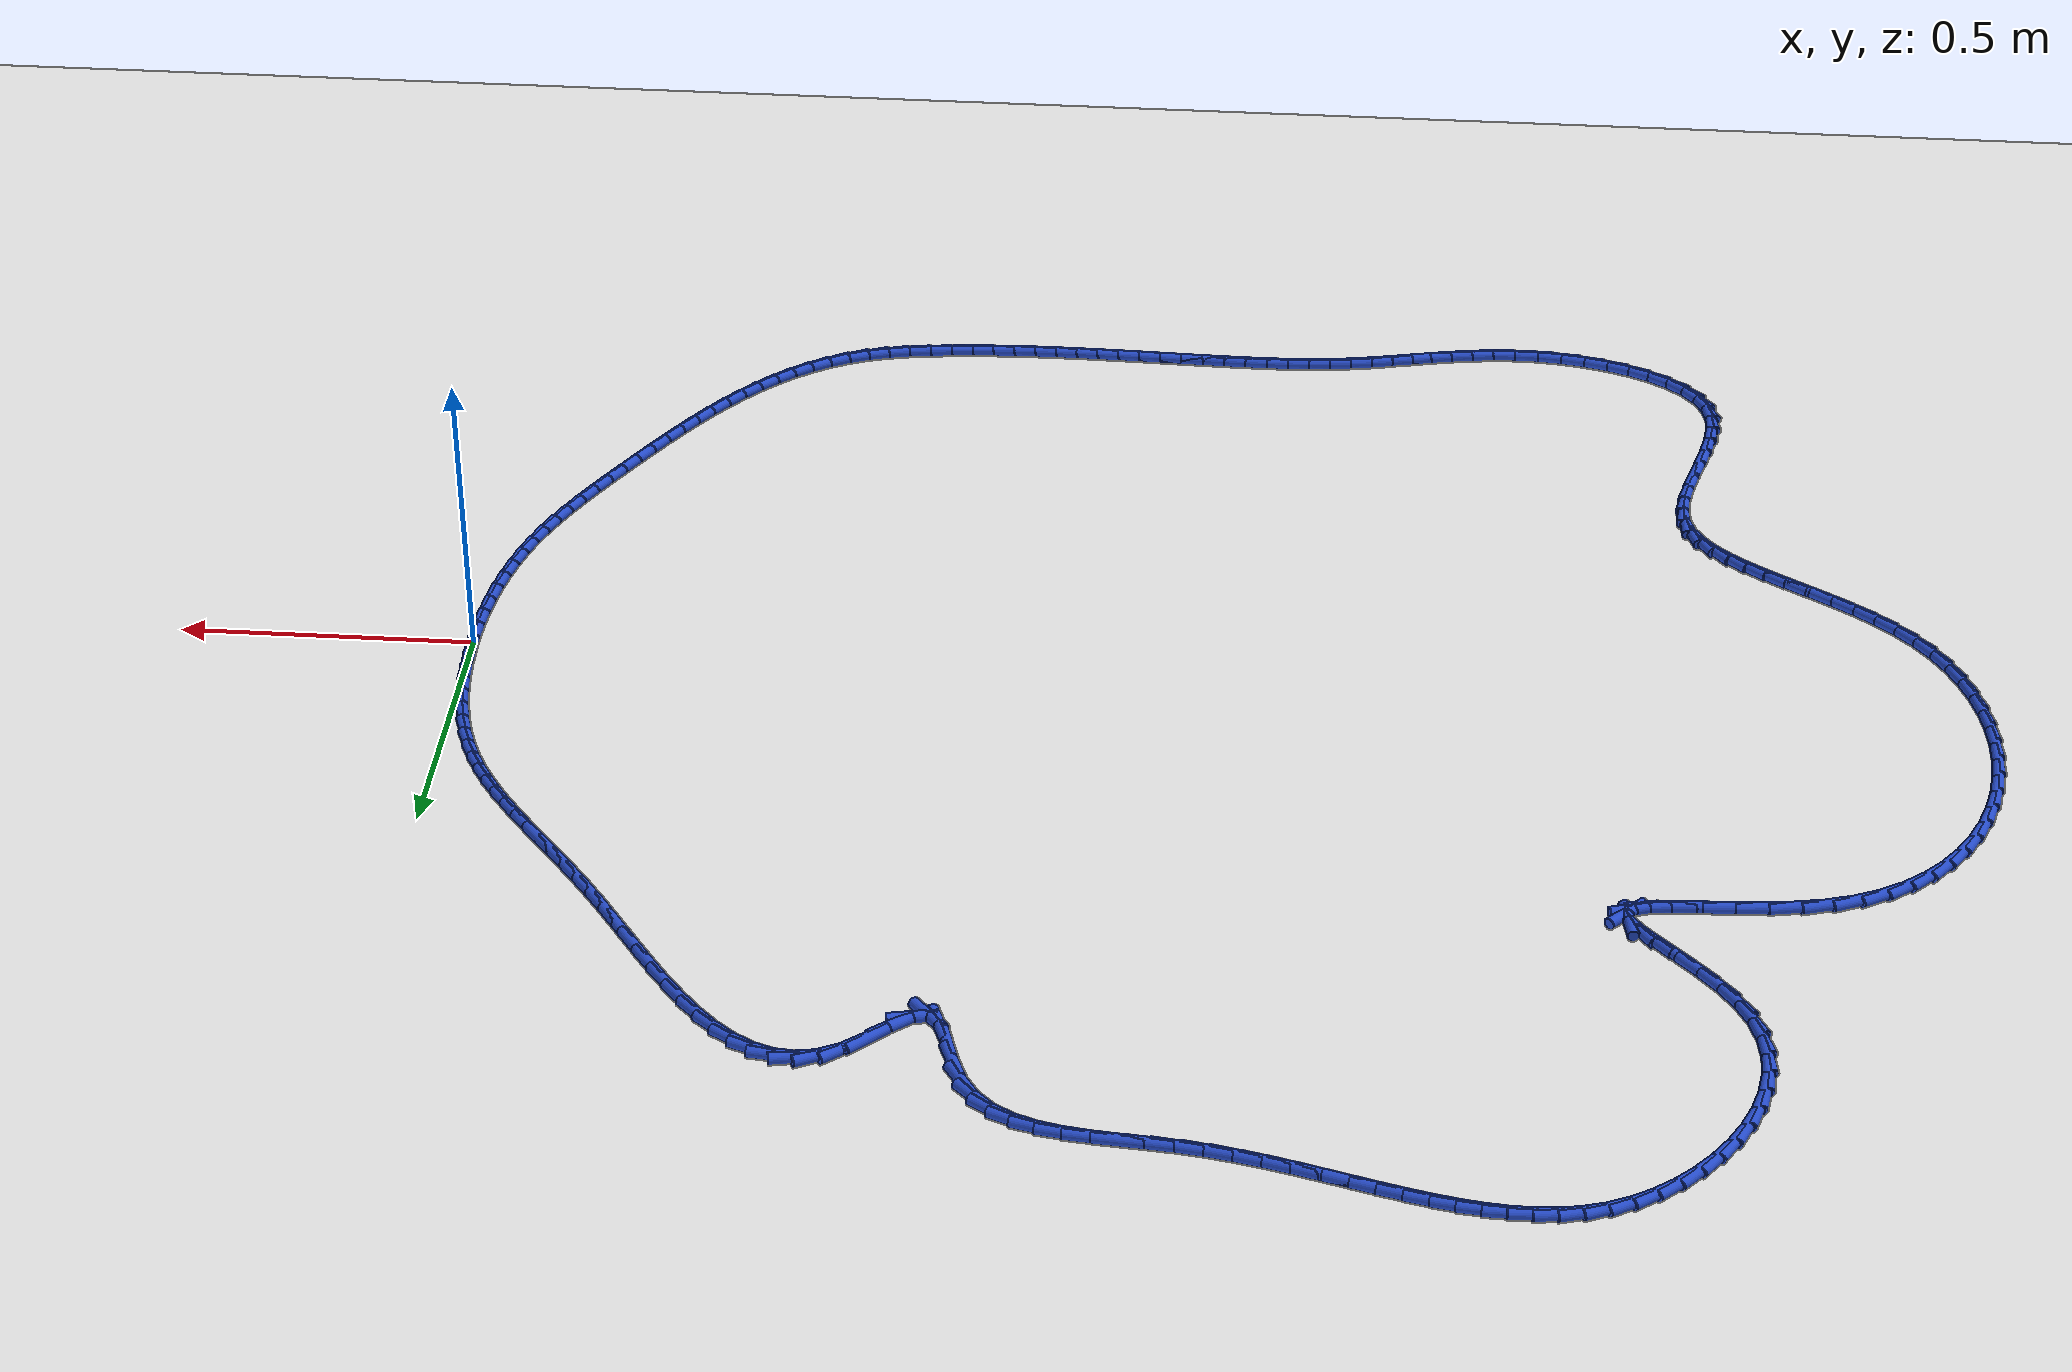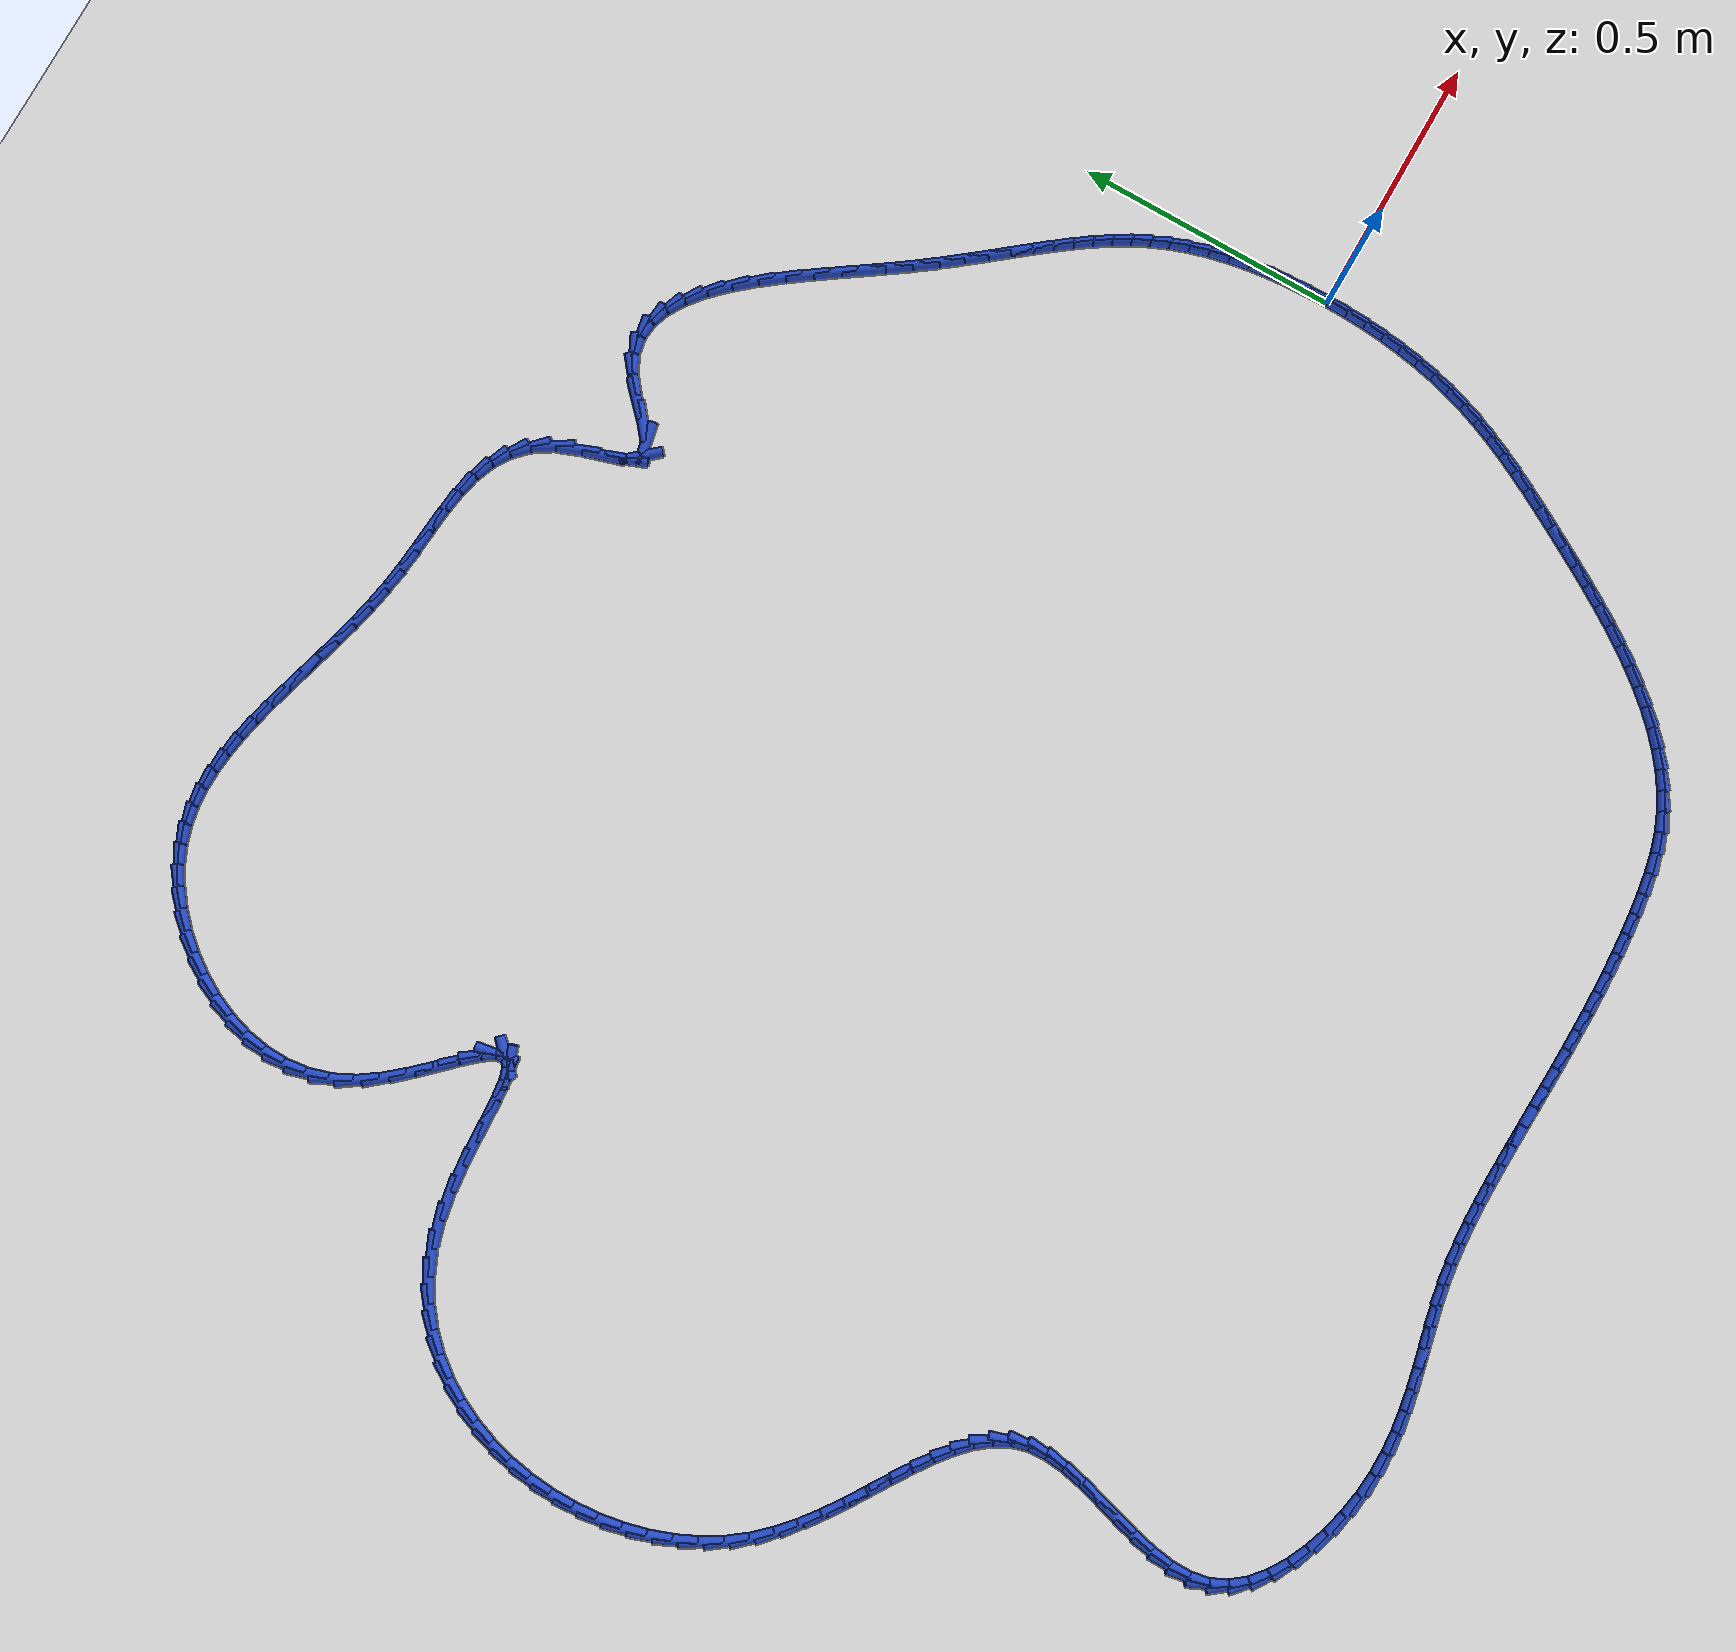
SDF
<sdf version="1.6">
 <world name="default">
  <light name="sun" type="directional">
   <pose>0 0 10 0 -0 0</pose>
   <diffuse>0.8 0.8 0.8 1</diffuse>
   <specular>0.2 0.2 0.2 1</specular>
   <attenuation>
    <range>1000</range>
    <constant>0.9</constant>
    <linear>0.01</linear>
    <quadratic>0.001</quadratic>
   </attenuation>
   <direction>-0.5 0.1 -0.9</direction>
  </light>
  <model name="ground_plane">
   <static>1</static>
   <link name="link">
    <collision name="collision">
     <geometry><plane><normal>0 0 1</normal><size>100 100</size></plane></geometry>
     <surface><friction><ode><mu>100</mu><mu2>50</mu2></ode></friction></surface>
    </collision>
    <visual name="visual">
     <cast_shadows>0</cast_shadows>
     <geometry><plane><normal>0 0 1</normal><size>100 100</size></plane></geometry>
     <material>
      <script><uri>file://media/materials/scripts/gazebo.material</uri><name>Gazebo/WhiteGlow</name></script>
     </material>
    </visual>
   </link>
  </model>
  <gravity>0 0 -9.8</gravity>
  <magnetic_field>6e-06 2.3e-05 -4.2e-05</magnetic_field>
  <atmosphere type="adiabatic"/>
  <physics name="default_physics" default="0" type="ode">
   <max_step_size>0.001</max_step_size>
   <real_time_factor>1</real_time_factor>
   <real_time_update_rate>1000</real_time_update_rate>
  </physics>
  <scene><ambient>0.4 0.4 0.4 1</ambient><background>0.7 0.7 0.7 1</background><shadows>1</shadows></scene>
  <spherical_coordinates>
   <surface_model>EARTH_WGS84</surface_model>
   <latitude_deg>0</latitude_deg>
   <longitude_deg>0</longitude_deg>
   <elevation>0</elevation>
   <heading_deg>0</heading_deg>
  </spherical_coordinates>
  <model name="line">
   <link name="link_0">
    <pose>0.0 8.326672684688674e-17 0.01 0 1.57 -1.5583323516176184</pose>
    <collision name="collision">
     <geometry><cylinder><radius>0.01</radius><length>0.08</length></cylinder></geometry>
    </collision>
    <visual name="visual">
     <material>
      <script><name>Gazebo/Blue</name><uri>file://media/materials/scripts/gazebo.material</uri></script>
     </material>
     <geometry><cylinder><radius>0.01</radius><length>0.08</length></cylinder></geometry>
    </visual>
   </link>
   <link name="link_1">
    <pose>-0.00049817348563206 0.039966999378888604 0.01 0 1.57 -1.5231837299847661</pose>
    <collision name="collision">
     <geometry><cylinder><radius>0.01</radius><length>0.08</length></cylinder></geometry>
    </collision>
    <visual name="visual">
     <material>
      <script><name>Gazebo/Blue</name><uri>file://media/materials/scripts/gazebo.material</uri></script>
     </material>
     <geometry><cylinder><radius>0.01</radius><length>0.08</length></cylinder></geometry>
    </visual>
   </link>
   <link name="link_2">
    <pose>-0.0024028264487304237 0.0799398976470006 0.01 0 1.57 -1.4854096803634396</pose>
    <collision name="collision">
     <geometry><cylinder><radius>0.01</radius><length>0.08</length></cylinder></geometry>
    </collision>
    <visual name="visual">
     <material>
      <script><name>Gazebo/Blue</name><uri>file://media/materials/scripts/gazebo.material</uri></script>
     </material>
     <geometry><cylinder><radius>0.01</radius><length>0.08</length></cylinder></geometry>
    </visual>
   </link>
   <link name="link_3">
    <pose>-0.005801826759930556 0.11965027237062047 0.01 0 1.57 -1.4443362459925622</pose>
    <collision name="collision">
     <geometry><cylinder><radius>0.01</radius><length>0.08</length></cylinder></geometry>
    </collision>
    <visual name="visual">
     <material>
      <script><name>Gazebo/Blue</name><uri>file://media/materials/scripts/gazebo.material</uri></script>
     </material>
     <geometry><cylinder><radius>0.01</radius><length>0.08</length></cylinder></geometry>
    </visual>
   </link>
   <link name="link_4">
    <pose>-0.01078304228986793 0.1588297011160325 0.01 0 1.57 -1.3991997554756217</pose>
    <collision name="collision">
     <geometry><cylinder><radius>0.01</radius><length>0.08</length></cylinder></geometry>
    </collision>
    <visual name="visual">
     <material>
      <script><name>Gazebo/Blue</name><uri>file://media/materials/scripts/gazebo.material</uri></script>
     </material>
     <geometry><cylinder><radius>0.01</radius><length>0.08</length></cylinder></geometry>
    </visual>
   </link>
   <link name="link_5">
    <pose>-0.017434340909178024 0.19720976144952124 0.01 0 1.57 -1.3491250632339262</pose>
    <collision name="collision">
     <geometry><cylinder><radius>0.01</radius><length>0.08</length></cylinder></geometry>
    </collision>
    <visual name="visual">
     <material>
      <script><name>Gazebo/Blue</name><uri>file://media/materials/scripts/gazebo.material</uri></script>
     </material>
     <geometry><cylinder><radius>0.01</radius><length>0.08</length></cylinder></geometry>
    </visual>
   </link>
   <link name="link_6">
    <pose>-0.025843590488496312 0.23452203093737095 0.01 0 1.57 -1.2931085205411417</pose>
    <collision name="collision">
     <geometry><cylinder><radius>0.01</radius><length>0.08</length></cylinder></geometry>
    </collision>
    <visual name="visual">
     <material>
      <script><name>Gazebo/Blue</name><uri>file://media/materials/scripts/gazebo.material</uri></script>
     </material>
     <geometry><cylinder><radius>0.01</radius><length>0.08</length></cylinder></geometry>
    </visual>
   </link>
   <link name="link_7">
    <pose>-0.03609865889845826 0.2704980871458661 0.01 0 1.57 -1.2300622602418907</pose>
    <collision name="collision">
     <geometry><cylinder><radius>0.01</radius><length>0.08</length></cylinder></geometry>
    </collision>
    <visual name="visual">
     <material>
      <script><name>Gazebo/Blue</name><uri>file://media/materials/scripts/gazebo.material</uri></script>
     </material>
     <geometry><cylinder><radius>0.01</radius><length>0.08</length></cylinder></geometry>
    </visual>
   </link>
   <link name="link_8">
    <pose>-0.04828646433652158 0.30487224631225424 0.01 0 1.57 -1.16303455924778</pose>
    <collision name="collision">
     <geometry><cylinder><radius>0.01</radius><length>0.08</length></cylinder></geometry>
    </collision>
    <visual name="visual">
     <material>
      <script><name>Gazebo/Blue</name><uri>file://media/materials/scripts/gazebo.material</uri></script>
     </material>
     <geometry><cylinder><radius>0.01</radius><length>0.08</length></cylinder></geometry>
    </visual>
   </link>
   <link name="link_9">
    <pose>-0.06242022724012387 0.33759135454210576 0.01 0 1.57 -1.099979973276726</pose>
    <collision name="collision">
     <geometry><cylinder><radius>0.01</radius><length>0.08</length></cylinder></geometry>
    </collision>
    <visual name="visual">
     <material>
      <script><name>Gazebo/Blue</name><uri>file://media/materials/scripts/gazebo.material</uri></script>
     </material>
     <geometry><cylinder><radius>0.01</radius><length>0.08</length></cylinder></geometry>
    </visual>
   </link>
   <link name="link_10">
    <pose>-0.07838812001780793 0.3689628719014119 0.01 0 1.57 -1.0435981428654346</pose>
    <collision name="collision">
     <geometry><cylinder><radius>0.01</radius><length>0.08</length></cylinder></geometry>
    </collision>
    <visual name="visual">
     <material>
      <script><name>Gazebo/Blue</name><uri>file://media/materials/scripts/gazebo.material</uri></script>
     </material>
     <geometry><cylinder><radius>0.01</radius><length>0.08</length></cylinder></geometry>
    </visual>
   </link>
   <link name="link_11">
    <pose>-0.09606618652572865 0.3993292348196423 0.01 0 1.57 -0.9954414647999831</pose>
    <collision name="collision">
     <geometry><cylinder><radius>0.01</radius><length>0.08</length></cylinder></geometry>
    </collision>
    <visual name="visual">
     <material>
      <script><name>Gazebo/Blue</name><uri>file://media/materials/scripts/gazebo.material</uri></script>
     </material>
     <geometry><cylinder><radius>0.01</radius><length>0.08</length></cylinder></geometry>
    </visual>
   </link>
   <link name="link_12">
    <pose>-0.1153304706200408 0.42903287972626597 0.01 0 1.57 -0.9564662723145362</pose>
    <collision name="collision">
     <geometry><cylinder><radius>0.01</radius><length>0.08</length></cylinder></geometry>
    </collision>
    <visual name="visual">
     <material>
      <script><name>Gazebo/Blue</name><uri>file://media/materials/scripts/gazebo.material</uri></script>
     </material>
     <geometry><cylinder><radius>0.01</radius><length>0.08</length></cylinder></geometry>
    </visual>
   </link>
   <link name="link_13">
    <pose>-0.1360570161568993 0.4584162430507523 0.01 0 1.57 -0.9270621116328968</pose>
    <collision name="collision">
     <geometry><cylinder><radius>0.01</radius><length>0.08</length></cylinder></geometry>
    </collision>
    <visual name="visual">
     <material>
      <script><name>Gazebo/Blue</name><uri>file://media/materials/scripts/gazebo.material</uri></script>
     </material>
     <geometry><cylinder><radius>0.01</radius><length>0.08</length></cylinder></geometry>
    </visual>
   </link>
   <link name="link_14">
    <pose>-0.15812186699245898 0.4878217612225703 0.01 0 1.57 -0.907149144727668</pose>
    <collision name="collision">
     <geometry><cylinder><radius>0.01</radius><length>0.08</length></cylinder></geometry>
    </collision>
    <visual name="visual">
     <material>
      <script><name>Gazebo/Blue</name><uri>file://media/materials/scripts/gazebo.material</uri></script>
     </material>
     <geometry><cylinder><radius>0.01</radius><length>0.08</length></cylinder></geometry>
    </visual>
   </link>
   <link name="link_15">
    <pose>-0.1814010669828746 0.5175918706711895 0.01 0 1.57 -0.8962978508619215</pose>
    <collision name="collision">
     <geometry><cylinder><radius>0.01</radius><length>0.08</length></cylinder></geometry>
    </collision>
    <visual name="visual">
     <material>
      <script><name>Gazebo/Blue</name><uri>file://media/materials/scripts/gazebo.material</uri></script>
     </material>
     <geometry><cylinder><radius>0.01</radius><length>0.08</length></cylinder></geometry>
    </visual>
   </link>
   <link name="link_16">
    <pose>-0.20577065998430114 0.5480690078260791 0.01 0 1.57 -0.8938399640405668</pose>
    <collision name="collision">
     <geometry><cylinder><radius>0.01</radius><length>0.08</length></cylinder></geometry>
    </collision>
    <visual name="visual">
     <material>
      <script><name>Gazebo/Blue</name><uri>file://media/materials/scripts/gazebo.material</uri></script>
     </material>
     <geometry><cylinder><radius>0.01</radius><length>0.08</length></cylinder></geometry>
    </visual>
   </link>
   <link name="link_17">
    <pose>-0.23110668985289326 0.5795956091167083 0.01 0 1.57 -0.8989571048070066</pose>
    <collision name="collision">
     <geometry><cylinder><radius>0.01</radius><length>0.08</length></cylinder></geometry>
    </collision>
    <visual name="visual">
     <material>
      <script><name>Gazebo/Blue</name><uri>file://media/materials/scripts/gazebo.material</uri></script>
     </material>
     <geometry><cylinder><radius>0.01</radius><length>0.08</length></cylinder></geometry>
    </visual>
   </link>
   <link name="link_18">
    <pose>-0.25728520044480596 0.6125141109725463 0.01 0 1.57 -0.9107459610765454</pose>
    <collision name="collision">
     <geometry><cylinder><radius>0.01</radius><length>0.08</length></cylinder></geometry>
    </collision>
    <visual name="visual">
     <material>
      <script><name>Gazebo/Blue</name><uri>file://media/materials/scripts/gazebo.material</uri></script>
     </material>
     <geometry><cylinder><radius>0.01</radius><length>0.08</length></cylinder></geometry>
    </visual>
   </link>
   <link name="link_19">
    <pose>-0.2841822356161941 0.6471669498230627 0.01 0 1.57 -0.9282648294291331</pose>
    <collision name="collision">
     <geometry><cylinder><radius>0.01</radius><length>0.08</length></cylinder></geometry>
    </collision>
    <visual name="visual">
     <material>
      <script><name>Gazebo/Blue</name><uri>file://media/materials/scripts/gazebo.material</uri></script>
     </material>
     <geometry><cylinder><radius>0.01</radius><length>0.08</length></cylinder></geometry>
    </visual>
   </link>
   <link name="link_20">
    <pose>-0.31167383922321235 0.6838965620977262 0.01 0 1.57 -0.950074335394609</pose>
    <collision name="collision">
     <geometry><cylinder><radius>0.01</radius><length>0.08</length></cylinder></geometry>
    </collision>
    <visual name="visual">
     <material>
      <script><name>Gazebo/Blue</name><uri>file://media/materials/scripts/gazebo.material</uri></script>
     </material>
     <geometry><cylinder><radius>0.01</radius><length>0.08</length></cylinder></geometry>
    </visual>
   </link>
   <link name="link_21">
    <pose>-0.33963944445947075 0.7230093221381866 0.01 0 1.57 -0.9664072503207561</pose>
    <collision name="collision">
     <geometry><cylinder><radius>0.01</radius><length>0.08</length></cylinder></geometry>
    </collision>
    <visual name="visual">
     <material>
      <script><name>Gazebo/Blue</name><uri>file://media/materials/scripts/gazebo.material</uri></script>
     </material>
     <geometry><cylinder><radius>0.01</radius><length>0.08</length></cylinder></geometry>
    </visual>
   </link>
   <link name="link_22">
    <pose>-0.3680243215104106 0.7641111076808196 0.01 0 1.57 -0.9702524257304159</pose>
    <collision name="collision">
     <geometry><cylinder><radius>0.01</radius><length>0.08</length></cylinder></geometry>
    </collision>
    <visual name="visual">
     <material>
      <script><name>Gazebo/Blue</name><uri>file://media/materials/scripts/gazebo.material</uri></script>
     </material>
     <geometry><cylinder><radius>0.01</radius><length>0.08</length></cylinder></geometry>
    </visual>
   </link>
   <link name="link_23">
    <pose>-0.3968334756852742 0.8061722228995774 0.01 0 1.57 -0.9622613198069169</pose>
    <collision name="collision">
     <geometry><cylinder><radius>0.01</radius><length>0.08</length></cylinder></geometry>
    </collision>
    <visual name="visual">
     <material>
      <script><name>Gazebo/Blue</name><uri>file://media/materials/scripts/gazebo.material</uri></script>
     </material>
     <geometry><cylinder><radius>0.01</radius><length>0.08</length></cylinder></geometry>
    </visual>
   </link>
   <link name="link_24">
    <pose>-0.4260740776370349 0.8481399330067232 0.01 0 1.57 -0.9421473699221572</pose>
    <collision name="collision">
     <geometry><cylinder><radius>0.01</radius><length>0.08</length></cylinder></geometry>
    </collision>
    <visual name="visual">
     <material>
      <script><name>Gazebo/Blue</name><uri>file://media/materials/scripts/gazebo.material</uri></script>
     </material>
     <geometry><cylinder><radius>0.01</radius><length>0.08</length></cylinder></geometry>
    </visual>
   </link>
   <link name="link_25">
    <pose>-0.45575329801866515 0.8889615032145198 0.01 0 1.57 -0.90838118942373</pose>
    <collision name="collision">
     <geometry><cylinder><radius>0.01</radius><length>0.08</length></cylinder></geometry>
    </collision>
    <visual name="visual">
     <material>
      <script><name>Gazebo/Blue</name><uri>file://media/materials/scripts/gazebo.material</uri></script>
     </material>
     <geometry><cylinder><radius>0.01</radius><length>0.08</length></cylinder></geometry>
    </visual>
   </link>
   <link name="link_26">
    <pose>-0.4858783074831382 0.9275841987352317 0.01 0 1.57 -0.8579496805630122</pose>
    <collision name="collision">
     <geometry><cylinder><radius>0.01</radius><length>0.08</length></cylinder></geometry>
    </collision>
    <visual name="visual">
     <material>
      <script><name>Gazebo/Blue</name><uri>file://media/materials/scripts/gazebo.material</uri></script>
     </material>
     <geometry><cylinder><radius>0.01</radius><length>0.08</length></cylinder></geometry>
    </visual>
   </link>
   <link name="link_27">
    <pose>-0.516456276683427 0.9629552847811216 0.01 0 1.57 -0.7858593543704875</pose>
    <collision name="collision">
     <geometry><cylinder><radius>0.01</radius><length>0.08</length></cylinder></geometry>
    </collision>
    <visual name="visual">
     <material>
      <script><name>Gazebo/Blue</name><uri>file://media/materials/scripts/gazebo.material</uri></script>
     </material>
     <geometry><cylinder><radius>0.01</radius><length>0.08</length></cylinder></geometry>
    </visual>
   </link>
   <link name="link_28">
    <pose>-0.5474943762725042 0.9940220265644525 0.01 0 1.57 -0.6844451093726458</pose>
    <collision name="collision">
     <geometry><cylinder><radius>0.01</radius><length>0.08</length></cylinder></geometry>
    </collision>
    <visual name="visual">
     <material>
      <script><name>Gazebo/Blue</name><uri>file://media/materials/scripts/gazebo.material</uri></script>
     </material>
     <geometry><cylinder><radius>0.01</radius><length>0.08</length></cylinder></geometry>
    </visual>
   </link>
   <link name="link_29">
    <pose>-0.5789997769033425 1.0197316892974875 0.01 0 1.57 -0.5429889634100166</pose>
    <collision name="collision">
     <geometry><cylinder><radius>0.01</radius><length>0.08</length></cylinder></geometry>
    </collision>
    <visual name="visual">
     <material>
      <script><name>Gazebo/Blue</name><uri>file://media/materials/scripts/gazebo.material</uri></script>
     </material>
     <geometry><cylinder><radius>0.01</radius><length>0.08</length></cylinder></geometry>
    </visual>
   </link>
   <link name="link_30">
    <pose>-0.6109796492289155 1.039031538192491 0.01 0 1.57 -0.3496716486804681</pose>
    <collision name="collision">
     <geometry><cylinder><radius>0.01</radius><length>0.08</length></cylinder></geometry>
    </collision>
    <visual name="visual">
     <material>
      <script><name>Gazebo/Blue</name><uri>file://media/materials/scripts/gazebo.material</uri></script>
     </material>
     <geometry><cylinder><radius>0.01</radius><length>0.08</length></cylinder></geometry>
    </visual>
   </link>
   <link name="link_31">
    <pose>-0.6434411639021953 1.050868838461725 0.01 0 1.57 -0.10047941065587637</pose>
    <collision name="collision">
     <geometry><cylinder><radius>0.01</radius><length>0.08</length></cylinder></geometry>
    </collision>
    <visual name="visual">
     <material>
      <script><name>Gazebo/Blue</name><uri>file://media/materials/scripts/gazebo.material</uri></script>
     </material>
     <geometry><cylinder><radius>0.01</radius><length>0.08</length></cylinder></geometry>
    </visual>
   </link>
   <link name="link_32">
    <pose>-0.6763914915761555 1.0541908553174542 0.01 0 1.57 0.18462051242492358</pose>
    <collision name="collision">
     <geometry><cylinder><radius>0.01</radius><length>0.08</length></cylinder></geometry>
    </collision>
    <visual name="visual">
     <material>
      <script><name>Gazebo/Blue</name><uri>file://media/materials/scripts/gazebo.material</uri></script>
     </material>
     <geometry><cylinder><radius>0.01</radius><length>0.08</length></cylinder></geometry>
    </visual>
   </link>
   <link name="link_33">
    <pose>-0.7098378029037689 1.0479448539719405 0.01 0 1.57 0.46109992126042093</pose>
    <collision name="collision">
     <geometry><cylinder><radius>0.01</radius><length>0.08</length></cylinder></geometry>
    </collision>
    <visual name="visual">
     <material>
      <script><name>Gazebo/Blue</name><uri>file://media/materials/scripts/gazebo.material</uri></script>
     </material>
     <geometry><cylinder><radius>0.01</radius><length>0.08</length></cylinder></geometry>
    </visual>
   </link>
   <link name="link_34">
    <pose>-0.7437872685380078 1.0310780996374482 0.01 0 1.57 0.6827527447862716</pose>
    <collision name="collision">
     <geometry><cylinder><radius>0.01</radius><length>0.08</length></cylinder></geometry>
    </collision>
    <visual name="visual">
     <material>
      <script><name>Gazebo/Blue</name><uri>file://media/materials/scripts/gazebo.material</uri></script>
     </material>
     <geometry><cylinder><radius>0.01</radius><length>0.08</length></cylinder></geometry>
    </visual>
   </link>
   <link name="link_35">
    <pose>-0.7781378011379877 1.0031434083678188 0.01 0 1.57 0.7666449596925557</pose>
    <collision name="collision">
     <geometry><cylinder><radius>0.01</radius><length>0.08</length></cylinder></geometry>
    </collision>
    <visual name="visual">
     <material>
      <script><name>Gazebo/Blue</name><uri>file://media/materials/scripts/gazebo.material</uri></script>
     </material>
     <geometry><cylinder><radius>0.01</radius><length>0.08</length></cylinder></geometry>
    </visual>
   </link>
   <link name="link_36">
    <pose>-0.811460425688177 0.9710477304059804 0.01 0 1.57 0.6841420462492547</pose>
    <collision name="collision">
     <geometry><cylinder><radius>0.01</radius><length>0.08</length></cylinder></geometry>
    </collision>
    <visual name="visual">
     <material>
      <script><name>Gazebo/Blue</name><uri>file://media/materials/scripts/gazebo.material</uri></script>
     </material>
     <geometry><cylinder><radius>0.01</radius><length>0.08</length></cylinder></geometry>
    </visual>
   </link>
   <link name="link_37">
    <pose>-0.8414423627658422 0.9465964081735322 0.01 0 1.57 0.20033806602521045</pose>
    <collision name="collision">
     <geometry><cylinder><radius>0.01</radius><length>0.08</length></cylinder></geometry>
    </collision>
    <visual name="visual">
     <material>
      <script><name>Gazebo/Blue</name><uri>file://media/materials/scripts/gazebo.material</uri></script>
     </material>
     <geometry><cylinder><radius>0.01</radius><length>0.08</length></cylinder></geometry>
    </visual>
   </link>
   <link name="link_38">
    <pose>-0.8657614808621669 0.9416581189948933 0.01 0 1.57 -0.8511530641034339</pose>
    <collision name="collision">
     <geometry><cylinder><radius>0.01</radius><length>0.08</length></cylinder></geometry>
    </collision>
    <visual name="visual">
     <material>
      <script><name>Gazebo/Blue</name><uri>file://media/materials/scripts/gazebo.material</uri></script>
     </material>
     <geometry><cylinder><radius>0.01</radius><length>0.08</length></cylinder></geometry>
    </visual>
   </link>
   <link name="link_39">
    <pose>-0.8836693353677442 0.9620906837110765 0.01 0 1.57 -1.2094232574247654</pose>
    <collision name="collision">
     <geometry><cylinder><radius>0.01</radius><length>0.08</length></cylinder></geometry>
    </collision>
    <visual name="visual">
     <material>
      <script><name>Gazebo/Blue</name><uri>file://media/materials/scripts/gazebo.material</uri></script>
     </material>
     <geometry><cylinder><radius>0.01</radius><length>0.08</length></cylinder></geometry>
    </visual>
   </link>
   <link name="link_40">
    <pose>-0.8980097063884424 1.0000310570697595 0.01 0 1.57 -1.2710924141885263</pose>
    <collision name="collision">
     <geometry><cylinder><radius>0.01</radius><length>0.08</length></cylinder></geometry>
    </collision>
    <visual name="visual">
     <material>
      <script><name>Gazebo/Blue</name><uri>file://media/materials/scripts/gazebo.material</uri></script>
     </material>
     <geometry><cylinder><radius>0.01</radius><length>0.08</length></cylinder></geometry>
    </visual>
   </link>
   <link name="link_41">
    <pose>-0.9121252516673028 1.0457106801608802 0.01 0 1.57 -1.194994764128867</pose>
    <collision name="collision">
     <geometry><cylinder><radius>0.01</radius><length>0.08</length></cylinder></geometry>
    </collision>
    <visual name="visual">
     <material>
      <script><name>Gazebo/Blue</name><uri>file://media/materials/scripts/gazebo.material</uri></script>
     </material>
     <geometry><cylinder><radius>0.01</radius><length>0.08</length></cylinder></geometry>
    </visual>
   </link>
   <link name="link_42">
    <pose>-0.9293533391948237 1.0893755460519343 0.01 0 1.57 -0.9986970327232371</pose>
    <collision name="collision">
     <geometry><cylinder><radius>0.01</radius><length>0.08</length></cylinder></geometry>
    </collision>
    <visual name="visual">
     <material>
      <script><name>Gazebo/Blue</name><uri>file://media/materials/scripts/gazebo.material</uri></script>
     </material>
     <geometry><cylinder><radius>0.01</radius><length>0.08</length></cylinder></geometry>
    </visual>
   </link>
   <link name="link_43">
    <pose>-0.95189871455113 1.1243874638641287 0.01 0 1.57 -0.7697768503113064</pose>
    <collision name="collision">
     <geometry><cylinder><radius>0.01</radius><length>0.08</length></cylinder></geometry>
    </collision>
    <visual name="visual">
     <material>
      <script><name>Gazebo/Blue</name><uri>file://media/materials/scripts/gazebo.material</uri></script>
     </material>
     <geometry><cylinder><radius>0.01</radius><length>0.08</length></cylinder></geometry>
    </visual>
   </link>
   <link name="link_44">
    <pose>-0.9794335731874988 1.1510752250739722 0.01 0 1.57 -0.5524647746519411</pose>
    <collision name="collision">
     <geometry><cylinder><radius>0.01</radius><length>0.08</length></cylinder></geometry>
    </collision>
    <visual name="visual">
     <material>
      <script><name>Gazebo/Blue</name><uri>file://media/materials/scripts/gazebo.material</uri></script>
     </material>
     <geometry><cylinder><radius>0.01</radius><length>0.08</length></cylinder></geometry>
    </visual>
   </link>
   <link name="link_45">
    <pose>-1.011286582800095 1.1707126574599886 0.01 0 1.57 -0.3722471770734209</pose>
    <collision name="collision">
     <geometry><cylinder><radius>0.01</radius><length>0.08</length></cylinder></geometry>
    </collision>
    <visual name="visual">
     <material>
      <script><name>Gazebo/Blue</name><uri>file://media/materials/scripts/gazebo.material</uri></script>
     </material>
     <geometry><cylinder><radius>0.01</radius><length>0.08</length></cylinder></geometry>
    </visual>
   </link>
   <link name="link_46">
    <pose>-1.0467864110850822 1.184573588800702 0.01 0 1.57 -0.2385945440334282</pose>
    <collision name="collision">
     <geometry><cylinder><radius>0.01</radius><length>0.08</length></cylinder></geometry>
    </collision>
    <visual name="visual">
     <material>
      <script><name>Gazebo/Blue</name><uri>file://media/materials/scripts/gazebo.material</uri></script>
     </material>
     <geometry><cylinder><radius>0.01</radius><length>0.08</length></cylinder></geometry>
    </visual>
   </link>
   <link name="link_47">
    <pose>-1.0852617257386246 1.1939318468746365 0.01 0 1.57 -0.14918953065308801</pose>
    <collision name="collision">
     <geometry><cylinder><radius>0.01</radius><length>0.08</length></cylinder></geometry>
    </collision>
    <visual name="visual">
     <material>
      <script><name>Gazebo/Blue</name><uri>file://media/materials/scripts/gazebo.material</uri></script>
     </material>
     <geometry><cylinder><radius>0.01</radius><length>0.08</length></cylinder></geometry>
    </visual>
   </link>
   <link name="link_48">
    <pose>-1.1260411944568873 1.200061259460316 0.01 0 1.57 -0.09810819162039007</pose>
    <collision name="collision">
     <geometry><cylinder><radius>0.01</radius><length>0.08</length></cylinder></geometry>
    </collision>
    <visual name="visual">
     <material>
      <script><name>Gazebo/Blue</name><uri>file://media/materials/scripts/gazebo.material</uri></script>
     </material>
     <geometry><cylinder><radius>0.01</radius><length>0.08</length></cylinder></geometry>
    </visual>
   </link>
   <link name="link_49">
    <pose>-1.1684534849360333 1.2042356543362638 0.01 0 1.57 -0.08036379602253131</pose>
    <collision name="collision">
     <geometry><cylinder><radius>0.01</radius><length>0.08</length></cylinder></geometry>
    </collision>
    <visual name="visual">
     <material>
      <script><name>Gazebo/Blue</name><uri>file://media/materials/scripts/gazebo.material</uri></script>
     </material>
     <geometry><cylinder><radius>0.01</radius><length>0.08</length></cylinder></geometry>
    </visual>
   </link>
   <link name="link_50">
    <pose>-1.211827264872227 1.2077288592810043 0.01 0 1.57 -0.09330307324138314</pose>
    <collision name="collision">
     <geometry><cylinder><radius>0.01</radius><length>0.08</length></cylinder></geometry>
    </collision>
    <visual name="visual">
     <material>
      <script><name>Gazebo/Blue</name><uri>file://media/materials/scripts/gazebo.material</uri></script>
     </material>
     <geometry><cylinder><radius>0.01</radius><length>0.08</length></cylinder></geometry>
    </visual>
   </link>
   <link name="link_51">
    <pose>-1.255491201961633 1.2118147020730614 0.01 0 1.57 -0.1346932216754523</pose>
    <collision name="collision">
     <geometry><cylinder><radius>0.01</radius><length>0.08</length></cylinder></geometry>
    </collision>
    <visual name="visual">
     <material>
      <script><name>Gazebo/Blue</name><uri>file://media/materials/scripts/gazebo.material</uri></script>
     </material>
     <geometry><cylinder><radius>0.01</radius><length>0.08</length></cylinder></geometry>
    </visual>
   </link>
   <link name="link_52">
    <pose>-1.2988063591727415 1.2176845002956824 0.01 0 1.57 -0.1820857939323398</pose>
    <collision name="collision">
     <geometry><cylinder><radius>0.01</radius><length>0.08</length></cylinder></geometry>
    </collision>
    <visual name="visual">
     <material>
      <script><name>Gazebo/Blue</name><uri>file://media/materials/scripts/gazebo.material</uri></script>
     </material>
     <geometry><cylinder><radius>0.01</radius><length>0.08</length></cylinder></geometry>
    </visual>
   </link>
   <link name="link_53">
    <pose>-1.3415188162616565 1.2255489404693147 0.01 0 1.57 -0.2202382557159246</pose>
    <collision name="collision">
     <geometry><cylinder><radius>0.01</radius><length>0.08</length></cylinder></geometry>
    </collision>
    <visual name="visual">
     <material>
      <script><name>Gazebo/Blue</name><uri>file://media/materials/scripts/gazebo.material</uri></script>
     </material>
     <geometry><cylinder><radius>0.01</radius><length>0.08</length></cylinder></geometry>
    </visual>
   </link>
   <link name="link_54">
    <pose>-1.3836271092575863 1.2349757073768912 0.01 0 1.57 -0.24880306063134558</pose>
    <collision name="collision">
     <geometry><cylinder><radius>0.01</radius><length>0.08</length></cylinder></geometry>
    </collision>
    <visual name="visual">
     <material>
      <script><name>Gazebo/Blue</name><uri>file://media/materials/scripts/gazebo.material</uri></script>
     </material>
     <geometry><cylinder><radius>0.01</radius><length>0.08</length></cylinder></geometry>
    </visual>
   </link>
   <link name="link_55">
    <pose>-1.4251341679413911 1.245521294992301 0.01 0 1.57 -0.26770692192413775</pose>
    <collision name="collision">
     <geometry><cylinder><radius>0.01</radius><length>0.08</length></cylinder></geometry>
    </collision>
    <visual name="visual">
     <material>
      <script><name>Gazebo/Blue</name><uri>file://media/materials/scripts/gazebo.material</uri></script>
     </material>
     <geometry><cylinder><radius>0.01</radius><length>0.08</length></cylinder></geometry>
    </visual>
   </link>
   <link name="link_56">
    <pose>-1.4660429220939306 1.2567421972894324 0.01 0 1.57 -0.27679922250770833</pose>
    <collision name="collision">
     <geometry><cylinder><radius>0.01</radius><length>0.08</length></cylinder></geometry>
    </collision>
    <visual name="visual">
     <material>
      <script><name>Gazebo/Blue</name><uri>file://media/materials/scripts/gazebo.material</uri></script>
     </material>
     <geometry><cylinder><radius>0.01</radius><length>0.08</length></cylinder></geometry>
    </visual>
   </link>
   <link name="link_57">
    <pose>-1.506356301496063 1.2681949082421742 0.01 0 1.57 -0.2757881766289168</pose>
    <collision name="collision">
     <geometry><cylinder><radius>0.01</radius><length>0.08</length></cylinder></geometry>
    </collision>
    <visual name="visual">
     <material>
      <script><name>Gazebo/Blue</name><uri>file://media/materials/scripts/gazebo.material</uri></script>
     </material>
     <geometry><cylinder><radius>0.01</radius><length>0.08</length></cylinder></geometry>
    </visual>
   </link>
   <link name="link_58">
    <pose>-1.5460772359286474 1.2794359218244151 0.01 0 1.57 -0.2641959303812687</pose>
    <collision name="collision">
     <geometry><cylinder><radius>0.01</radius><length>0.08</length></cylinder></geometry>
    </collision>
    <visual name="visual">
     <material>
      <script><name>Gazebo/Blue</name><uri>file://media/materials/scripts/gazebo.material</uri></script>
     </material>
     <geometry><cylinder><radius>0.01</radius><length>0.08</length></cylinder></geometry>
    </visual>
   </link>
   <link name="link_59">
    <pose>-1.585208655172544 1.2900217320100436 0.01 0 1.57 -0.24133449417910988</pose>
    <collision name="collision">
     <geometry><cylinder><radius>0.01</radius><length>0.08</length></cylinder></geometry>
    </collision>
    <visual name="visual">
     <material>
      <script><name>Gazebo/Blue</name><uri>file://media/materials/scripts/gazebo.material</uri></script>
     </material>
     <geometry><cylinder><radius>0.01</radius><length>0.08</length></cylinder></geometry>
    </visual>
   </link>
   <link name="link_60">
    <pose>-1.6237534890086112 1.2995088327729485 0.01 0 1.57 -0.2063118415825362</pose>
    <collision name="collision">
     <geometry><cylinder><radius>0.01</radius><length>0.08</length></cylinder></geometry>
    </collision>
    <visual name="visual">
     <material>
      <script><name>Gazebo/Blue</name><uri>file://media/materials/scripts/gazebo.material</uri></script>
     </material>
     <geometry><cylinder><radius>0.01</radius><length>0.08</length></cylinder></geometry>
    </visual>
   </link>
   <link name="link_61">
    <pose>-1.6617146672177074 1.3074537180870176 0.01 0 1.57 -0.15808896118092197</pose>
    <collision name="collision">
     <geometry><cylinder><radius>0.01</radius><length>0.08</length></cylinder></geometry>
    </collision>
    <visual name="visual">
     <material>
      <script><name>Gazebo/Blue</name><uri>file://media/materials/scripts/gazebo.material</uri></script>
     </material>
     <geometry><cylinder><radius>0.01</radius><length>0.08</length></cylinder></geometry>
    </visual>
   </link>
   <link name="link_62">
    <pose>-1.6990951195806927 1.3134128819261404 0.01 0 1.57 -0.09562274098867192</pose>
    <collision name="collision">
     <geometry><cylinder><radius>0.01</radius><length>0.08</length></cylinder></geometry>
    </collision>
    <visual name="visual">
     <material>
      <script><name>Gazebo/Blue</name><uri>file://media/materials/scripts/gazebo.material</uri></script>
     </material>
     <geometry><cylinder><radius>0.01</radius><length>0.08</length></cylinder></geometry>
    </visual>
   </link>
   <link name="link_63">
    <pose>-1.7358977758784264 1.3169428182642056 0.01 0 1.57 -0.018138857817500083</pose>
    <collision name="collision">
     <geometry><cylinder><radius>0.01</radius><length>0.08</length></cylinder></geometry>
    </collision>
    <visual name="visual">
     <material>
      <script><name>Gazebo/Blue</name><uri>file://media/materials/scripts/gazebo.material</uri></script>
     </material>
     <geometry><cylinder><radius>0.01</radius><length>0.08</length></cylinder></geometry>
    </visual>
   </link>
   <link name="link_64">
    <pose>-1.7721255658917667 1.3176000210751013 0.01 0 1.57 0.07443725250544697</pose>
    <collision name="collision">
     <geometry><cylinder><radius>0.01</radius><length>0.08</length></cylinder></geometry>
    </collision>
    <visual name="visual">
     <material>
      <script><name>Gazebo/Blue</name><uri>file://media/materials/scripts/gazebo.material</uri></script>
     </material>
     <geometry><cylinder><radius>0.01</radius><length>0.08</length></cylinder></geometry>
    </visual>
   </link>
   <link name="link_65">
    <pose>-1.8077814194015736 1.314940984332716 0.01 0 1.57 0.18093905527176934</pose>
    <collision name="collision">
     <geometry><cylinder><radius>0.01</radius><length>0.08</length></cylinder></geometry>
    </collision>
    <visual name="visual">
     <material>
      <script><name>Gazebo/Blue</name><uri>file://media/materials/scripts/gazebo.material</uri></script>
     </material>
     <geometry><cylinder><radius>0.01</radius><length>0.08</length></cylinder></geometry>
    </visual>
   </link>
   <link name="link_66">
    <pose>-1.8428682661887064 1.308522202010939 0.01 0 1.57 0.298505774573779</pose>
    <collision name="collision">
     <geometry><cylinder><radius>0.01</radius><length>0.08</length></cylinder></geometry>
    </collision>
    <visual name="visual">
     <material>
      <script><name>Gazebo/Blue</name><uri>file://media/materials/scripts/gazebo.material</uri></script>
     </material>
     <geometry><cylinder><radius>0.01</radius><length>0.08</length></cylinder></geometry>
    </visual>
   </link>
   <link name="link_67">
    <pose>-1.8773890360340229 1.2979001680836582 0.01 0 1.57 0.42255659736771134</pose>
    <collision name="collision">
     <geometry><cylinder><radius>0.01</radius><length>0.08</length></cylinder></geometry>
    </collision>
    <visual name="visual">
     <material>
      <script><name>Gazebo/Blue</name><uri>file://media/materials/scripts/gazebo.material</uri></script>
     </material>
     <geometry><cylinder><radius>0.01</radius><length>0.08</length></cylinder></geometry>
    </visual>
   </link>
   <link name="link_68">
    <pose>-1.911346657957439 1.2826313777290375 0.01 0 1.57 0.5451701905245984</pose>
    <collision name="collision">
     <geometry><cylinder><radius>0.01</radius><length>0.08</length></cylinder></geometry>
    </collision>
    <visual name="visual">
     <material>
      <script><name>Gazebo/Blue</name><uri>file://media/materials/scripts/gazebo.material</uri></script>
     </material>
     <geometry><cylinder><radius>0.01</radius><length>0.08</length></cylinder></geometry>
    </visual>
   </link>
   <link name="link_69">
    <pose>-1.9446372994509264 1.2624412875653537 0.01 0 1.57 0.6565397373517307</pose>
    <collision name="collision">
     <geometry><cylinder><radius>0.01</radius><length>0.08</length></cylinder></geometry>
    </collision>
    <visual name="visual">
     <material>
      <script><name>Gazebo/Blue</name><uri>file://media/materials/scripts/gazebo.material</uri></script>
     </material>
     <geometry><cylinder><radius>0.01</radius><length>0.08</length></cylinder></geometry>
    </visual>
   </link>
   <link name="link_70">
    <pose>-1.9767544843478186 1.237692580501354 0.01 0 1.57 0.7592291743797539</pose>
    <collision name="collision">
     <geometry><cylinder><radius>0.01</radius><length>0.08</length></cylinder></geometry>
    </collision>
    <visual name="visual">
     <material>
      <script><name>Gazebo/Blue</name><uri>file://media/materials/scripts/gazebo.material</uri></script>
     </material>
     <geometry><cylinder><radius>0.01</radius><length>0.08</length></cylinder></geometry>
    </visual>
   </link>
   <link name="link_71">
    <pose>-2.007096831347578 1.2088981368848986 0.01 0 1.57 0.8576048717542797</pose>
    <collision name="collision">
     <geometry><cylinder><radius>0.01</radius><length>0.08</length></cylinder></geometry>
    </collision>
    <visual name="visual">
     <material>
      <script><name>Gazebo/Blue</name><uri>file://media/materials/scripts/gazebo.material</uri></script>
     </material>
     <geometry><cylinder><radius>0.01</radius><length>0.08</length></cylinder></geometry>
    </visual>
   </link>
   <link name="link_72">
    <pose>-2.035062959149668 1.176570837063848 0.01 0 1.57 0.9554254708043374</pose>
    <collision name="collision">
     <geometry><cylinder><radius>0.01</radius><length>0.08</length></cylinder></geometry>
    </collision>
    <visual name="visual">
     <material>
      <script><name>Gazebo/Blue</name><uri>file://media/materials/scripts/gazebo.material</uri></script>
     </material>
     <geometry><cylinder><radius>0.01</radius><length>0.08</length></cylinder></geometry>
    </visual>
   </link>
   <link name="link_73">
    <pose>-2.0600514864535526 1.1412235613860628 0.01 0 1.57 1.056072839593738</pose>
    <collision name="collision">
     <geometry><cylinder><radius>0.01</radius><length>0.08</length></cylinder></geometry>
    </collision>
    <visual name="visual">
     <material>
      <script><name>Gazebo/Blue</name><uri>file://media/materials/scripts/gazebo.material</uri></script>
     </material>
     <geometry><cylinder><radius>0.01</radius><length>0.08</length></cylinder></geometry>
    </visual>
   </link>
   <link name="link_74">
    <pose>-2.081461031958693 1.1033691901994038 0.01 0 1.57 1.1627030110061976</pose>
    <collision name="collision">
     <geometry><cylinder><radius>0.01</radius><length>0.08</length></cylinder></geometry>
    </collision>
    <visual name="visual">
     <material>
      <script><name>Gazebo/Blue</name><uri>file://media/materials/scripts/gazebo.material</uri></script>
     </material>
     <geometry><cylinder><radius>0.01</radius><length>0.08</length></cylinder></geometry>
    </visual>
   </link>
   <link name="link_75">
    <pose>-2.098690214364553 1.0635206038517315 0.01 0 1.57 1.27826414009599</pose>
    <collision name="collision">
     <geometry><cylinder><radius>0.01</radius><length>0.08</length></cylinder></geometry>
    </collision>
    <visual name="visual">
     <material>
      <script><name>Gazebo/Blue</name><uri>file://media/materials/scripts/gazebo.material</uri></script>
     </material>
     <geometry><cylinder><radius>0.01</radius><length>0.08</length></cylinder></geometry>
    </visual>
   </link>
   <link name="link_76">
    <pose>-2.111137652370596 1.0221906826909055 0.01 0 1.57 1.405312220309387</pose>
    <collision name="collision">
     <geometry><cylinder><radius>0.01</radius><length>0.08</length></cylinder></geometry>
    </collision>
    <visual name="visual">
     <material>
      <script><name>Gazebo/Blue</name><uri>file://media/materials/scripts/gazebo.material</uri></script>
     </material>
     <geometry><cylinder><radius>0.01</radius><length>0.08</length></cylinder></geometry>
    </visual>
   </link>
   <link name="link_77">
    <pose>-2.118201964676284 0.9798923070647879 0.01 0 1.57 1.5455454247379714</pose>
    <collision name="collision">
     <geometry><cylinder><radius>0.01</radius><length>0.08</length></cylinder></geometry>
    </collision>
    <visual name="visual">
     <material>
      <script><name>Gazebo/Blue</name><uri>file://media/materials/scripts/gazebo.material</uri></script>
     </material>
     <geometry><cylinder><radius>0.01</radius><length>0.08</length></cylinder></geometry>
    </visual>
   </link>
   <link name="link_78">
    <pose>-2.119281769981081 0.9371383573212388 0.01 0 1.57 -1.4425459288353755</pose>
    <collision name="collision">
     <geometry><cylinder><radius>0.01</radius><length>0.08</length></cylinder></geometry>
    </collision>
    <visual name="visual">
     <material>
      <script><name>Gazebo/Blue</name><uri>file://media/materials/scripts/gazebo.material</uri></script>
     </material>
     <geometry><cylinder><radius>0.01</radius><length>0.08</length></cylinder></geometry>
    </visual>
   </link>
   <link name="link_79">
    <pose>-2.1137756869844493 0.8944417138081177 0.01 0 1.57 -1.278133128932933</pose>
    <collision name="collision">
     <geometry><cylinder><radius>0.01</radius><length>0.08</length></cylinder></geometry>
    </collision>
    <visual name="visual">
     <material>
      <script><name>Gazebo/Blue</name><uri>file://media/materials/scripts/gazebo.material</uri></script>
     </material>
     <geometry><cylinder><radius>0.01</radius><length>0.08</length></cylinder></geometry>
    </visual>
   </link>
   <link name="link_80">
    <pose>-2.1010823343858505 0.8523152568732862 0.01 0 1.57 -1.108243184468283</pose>
    <collision name="collision">
     <geometry><cylinder><radius>0.01</radius><length>0.08</length></cylinder></geometry>
    </collision>
    <visual name="visual">
     <material>
      <script><name>Gazebo/Blue</name><uri>file://media/materials/scripts/gazebo.material</uri></script>
     </material>
     <geometry><cylinder><radius>0.01</radius><length>0.08</length></cylinder></geometry>
    </visual>
   </link>
   <link name="link_81">
    <pose>-2.080616970885217 0.8112722908518365 0.01 0 1.57 -0.9617065921817991</pose>
    <collision name="collision">
     <geometry><cylinder><radius>0.01</radius><length>0.08</length></cylinder></geometry>
    </collision>
    <visual name="visual">
     <material>
      <script><name>Gazebo/Blue</name><uri>file://media/materials/scripts/gazebo.material</uri></script>
     </material>
     <geometry><cylinder><radius>0.01</radius><length>0.08</length></cylinder></geometry>
    </visual>
   </link>
   <link name="link_82">
    <pose>-2.053124340687858 0.7718599953710827 0.01 0 1.57 -0.867904822204166</pose>
    <collision name="collision">
     <geometry><cylinder><radius>0.01</radius><length>0.08</length></cylinder></geometry>
    </collision>
    <visual name="visual">
     <material>
      <script><name>Gazebo/Blue</name><uri>file://media/materials/scripts/gazebo.material</uri></script>
     </material>
     <geometry><cylinder><radius>0.01</radius><length>0.08</length></cylinder></geometry>
    </visual>
   </link>
   <link name="link_83">
    <pose>-2.0216268749019872 0.7346835855232764 0.01 0 1.57 -0.8165272662750818</pose>
    <collision name="collision">
     <geometry><cylinder><radius>0.01</radius><length>0.08</length></cylinder></geometry>
    </collision>
    <visual name="visual">
     <material>
      <script><name>Gazebo/Blue</name><uri>file://media/materials/scripts/gazebo.material</uri></script>
     </material>
     <geometry><cylinder><radius>0.01</radius><length>0.08</length></cylinder></geometry>
    </visual>
   </link>
   <link name="link_84">
    <pose>-1.9893706910978315 0.7003539759319802 0.01 0 1.57 -0.8035870891360066</pose>
    <collision name="collision">
     <geometry><cylinder><radius>0.01</radius><length>0.08</length></cylinder></geometry>
    </collision>
    <visual name="visual">
     <material>
      <script><name>Gazebo/Blue</name><uri>file://media/materials/scripts/gazebo.material</uri></script>
     </material>
     <geometry><cylinder><radius>0.01</radius><length>0.08</length></cylinder></geometry>
    </visual>
   </link>
   <link name="link_85">
    <pose>-1.9596019068456187 0.6694820812207571 0.01 0 1.57 -0.8397913096755745</pose>
    <collision name="collision">
     <geometry><cylinder><radius>0.01</radius><length>0.08</length></cylinder></geometry>
    </collision>
    <visual name="visual">
     <material>
      <script><name>Gazebo/Blue</name><uri>file://media/materials/scripts/gazebo.material</uri></script>
     </material>
     <geometry><cylinder><radius>0.01</radius><length>0.08</length></cylinder></geometry>
    </visual>
   </link>
   <link name="link_86">
    <pose>-1.9355666397155762 0.6426788160131706 0.01 0 1.57 -0.973264243758359</pose>
    <collision name="collision">
     <geometry><cylinder><radius>0.01</radius><length>0.08</length></cylinder></geometry>
    </collision>
    <visual name="visual">
     <material>
      <script><name>Gazebo/Blue</name><uri>file://media/materials/scripts/gazebo.material</uri></script>
     </material>
     <geometry><cylinder><radius>0.01</radius><length>0.08</length></cylinder></geometry>
    </visual>
   </link>
   <link name="link_87">
    <pose>-1.920511007277932 0.620555094932783 0.01 0 1.57 -1.4040120548253978</pose>
    <collision name="collision">
     <geometry><cylinder><radius>0.01</radius><length>0.08</length></cylinder></geometry>
    </collision>
    <visual name="visual">
     <material>
      <script><name>Gazebo/Blue</name><uri>file://media/materials/scripts/gazebo.material</uri></script>
     </material>
     <geometry><cylinder><radius>0.01</radius><length>0.08</length></cylinder></geometry>
    </visual>
   </link>
   <link name="link_88">
    <pose>-1.9176769089594785 0.6037203495169039 0.01 0 1.57 0.7963314833209875</pose>
    <collision name="collision">
     <geometry><cylinder><radius>0.01</radius><length>0.08</length></cylinder></geometry>
    </collision>
    <visual name="visual">
     <material>
      <script><name>Gazebo/Blue</name><uri>file://media/materials/scripts/gazebo.material</uri></script>
     </material>
     <geometry><cylinder><radius>0.01</radius><length>0.08</length></cylinder></geometry>
    </visual>
   </link>
   <link name="link_89">
    <pose>-1.9288705498859946 0.5922792256037586 0.01 0 1.57 0.29650184930600826</pose>
    <collision name="collision">
     <geometry><cylinder><radius>0.01</radius><length>0.08</length></cylinder></geometry>
    </collision>
    <visual name="visual">
     <material>
      <script><name>Gazebo/Blue</name><uri>file://media/materials/scripts/gazebo.material</uri></script>
     </material>
     <geometry><cylinder><radius>0.01</radius><length>0.08</length></cylinder></geometry>
    </visual>
   </link>
   <link name="link_90">
    <pose>-1.9523762090224026 0.5850980706292066 0.01 0 1.57 0.12566828416263573</pose>
    <collision name="collision">
     <geometry><cylinder><radius>0.01</radius><length>0.08</length></cylinder></geometry>
    </collision>
    <visual name="visual">
     <material>
      <script><name>Gazebo/Blue</name><uri>file://media/materials/scripts/gazebo.material</uri></script>
     </material>
     <geometry><cylinder><radius>0.01</radius><length>0.08</length></cylinder></geometry>
    </visual>
   </link>
   <link name="link_91">
    <pose>-1.9859479654082999 0.5808568153666116 0.01 0 1.57 0.0632473104853528</pose>
    <collision name="collision">
     <geometry><cylinder><radius>0.01</radius><length>0.08</length></cylinder></geometry>
    </collision>
    <visual name="visual">
     <material>
      <script><name>Gazebo/Blue</name><uri>file://media/materials/scripts/gazebo.material</uri></script>
     </material>
     <geometry><cylinder><radius>0.01</radius><length>0.08</length></cylinder></geometry>
    </visual>
   </link>
   <link name="link_92">
    <pose>-2.0273398980832846 0.5782353905893374 0.01 0 1.57 0.04939245278671325</pose>
    <collision name="collision">
     <geometry><cylinder><radius>0.01</radius><length>0.08</length></cylinder></geometry>
    </collision>
    <visual name="visual">
     <material>
      <script><name>Gazebo/Blue</name><uri>file://media/materials/scripts/gazebo.material</uri></script>
     </material>
     <geometry><cylinder><radius>0.01</radius><length>0.08</length></cylinder></geometry>
    </visual>
   </link>
   <link name="link_93">
    <pose>-2.0743060860869513 0.5759137270707475 0.01 0 1.57 0.06635048256645906</pose>
    <collision name="collision">
     <geometry><cylinder><radius>0.01</radius><length>0.08</length></cylinder></geometry>
    </collision>
    <visual name="visual">
     <material>
      <script><name>Gazebo/Blue</name><uri>file://media/materials/scripts/gazebo.material</uri></script>
     </material>
     <geometry><cylinder><radius>0.01</radius><length>0.08</length></cylinder></geometry>
    </visual>
   </link>
   <link name="link_94">
    <pose>-2.124600608458899 0.5725717555842054 0.01 0 1.57 0.11015346056883517</pose>
    <collision name="collision">
     <geometry><cylinder><radius>0.01</radius><length>0.08</length></cylinder></geometry>
    </collision>
    <visual name="visual">
     <material>
      <script><name>Gazebo/Blue</name><uri>file://media/materials/scripts/gazebo.material</uri></script>
     </material>
     <geometry><cylinder><radius>0.01</radius><length>0.08</length></cylinder></geometry>
    </visual>
   </link>
   <link name="link_95">
    <pose>-2.175977544238724 0.5668894069030745 0.01 0 1.57 0.18395812294698327</pose>
    <collision name="collision">
     <geometry><cylinder><radius>0.01</radius><length>0.08</length></cylinder></geometry>
    </collision>
    <visual name="visual">
     <material>
      <script><name>Gazebo/Blue</name><uri>file://media/materials/scripts/gazebo.material</uri></script>
     </material>
     <geometry><cylinder><radius>0.01</radius><length>0.08</length></cylinder></geometry>
    </visual>
   </link>
   <link name="link_96">
    <pose>-2.2261909724660227 0.5575466118007191 0.01 0 1.57 0.2942550114862895</pose>
    <collision name="collision">
     <geometry><cylinder><radius>0.01</radius><length>0.08</length></cylinder></geometry>
    </collision>
    <visual name="visual">
     <material>
      <script><name>Gazebo/Blue</name><uri>file://media/materials/scripts/gazebo.material</uri></script>
     </material>
     <geometry><cylinder><radius>0.01</radius><length>0.08</length></cylinder></geometry>
    </visual>
   </link>
   <link name="link_97">
    <pose>-2.2731239835218977 0.5433234395034396 0.01 0 1.57 0.4227066299343336</pose>
    <collision name="collision">
     <geometry><cylinder><radius>0.01</radius><length>0.08</length></cylinder></geometry>
    </collision>
    <visual name="visual">
     <material>
      <script><name>Gazebo/Blue</name><uri>file://media/materials/scripts/gazebo.material</uri></script>
     </material>
     <geometry><cylinder><radius>0.01</radius><length>0.08</length></cylinder></geometry>
    </visual>
   </link>
   <link name="link_98">
    <pose>-2.315997147198804 0.5240381091980478 0.01 0 1.57 0.5520699394514305</pose>
    <collision name="collision">
     <geometry><cylinder><radius>0.01</radius><length>0.08</length></cylinder></geometry>
    </collision>
    <visual name="visual">
     <material>
      <script><name>Gazebo/Blue</name><uri>file://media/materials/scripts/gazebo.material</uri></script>
     </material>
     <geometry><cylinder><radius>0.01</radius><length>0.08</length></cylinder></geometry>
    </visual>
   </link>
   <link name="link_99">
    <pose>-2.3548226372790286 0.5001232821657957 0.01 0 1.57 0.6793388754209444</pose>
    <collision name="collision">
     <geometry><cylinder><radius>0.01</radius><length>0.08</length></cylinder></geometry>
    </collision>
    <visual name="visual">
     <material>
      <script><name>Gazebo/Blue</name><uri>file://media/materials/scripts/gazebo.material</uri></script>
     </material>
     <geometry><cylinder><radius>0.01</radius><length>0.08</length></cylinder></geometry>
    </visual>
   </link>
   <link name="link_100">
    <pose>-2.3896229586753694 0.47201963869940017 0.01 0 1.57 0.8022222973451397</pose>
    <collision name="collision">
     <geometry><cylinder><radius>0.01</radius><length>0.08</length></cylinder></geometry>
    </collision>
    <visual name="visual">
     <material>
      <script><name>Gazebo/Blue</name><uri>file://media/materials/scripts/gazebo.material</uri></script>
     </material>
     <geometry><cylinder><radius>0.01</radius><length>0.08</length></cylinder></geometry>
    </visual>
   </link>
   <link name="link_101">
    <pose>-2.420420616300628 0.4401678590915779 0.01 0 1.57 0.9191887726935113</pose>
    <collision name="collision">
     <geometry><cylinder><radius>0.01</radius><length>0.08</length></cylinder></geometry>
    </collision>
    <visual name="visual">
     <material>
      <script><name>Gazebo/Blue</name><uri>file://media/materials/scripts/gazebo.material</uri></script>
     </material>
     <geometry><cylinder><radius>0.01</radius><length>0.08</length></cylinder></geometry>
    </visual>
   </link>
   <link name="link_102">
    <pose>-2.4472381150676026 0.4050086236350471 0.01 0 1.57 1.0295218484912654</pose>
    <collision name="collision">
     <geometry><cylinder><radius>0.01</radius><length>0.08</length></cylinder></geometry>
    </collision>
    <visual name="visual">
     <material>
      <script><name>Gazebo/Blue</name><uri>file://media/materials/scripts/gazebo.material</uri></script>
     </material>
     <geometry><cylinder><radius>0.01</radius><length>0.08</length></cylinder></geometry>
    </visual>
   </link>
   <link name="link_103">
    <pose>-2.470097959889092 0.36698261262252446 0.01 0 1.57 1.133214566473836</pose>
    <collision name="collision">
     <geometry><cylinder><radius>0.01</radius><length>0.08</length></cylinder></geometry>
    </collision>
    <visual name="visual">
     <material>
      <script><name>Gazebo/Blue</name><uri>file://media/materials/scripts/gazebo.material</uri></script>
     </material>
     <geometry><cylinder><radius>0.01</radius><length>0.08</length></cylinder></geometry>
    </visual>
   </link>
   <link name="link_104">
    <pose>-2.489022655677898 0.3265305063467271 0.01 0 1.57 1.2307893025706986</pose>
    <collision name="collision">
     <geometry><cylinder><radius>0.01</radius><length>0.08</length></cylinder></geometry>
    </collision>
    <visual name="visual">
     <material>
      <script><name>Gazebo/Blue</name><uri>file://media/materials/scripts/gazebo.material</uri></script>
     </material>
     <geometry><cylinder><radius>0.01</radius><length>0.08</length></cylinder></geometry>
    </visual>
   </link>
   <link name="link_105">
    <pose>-2.5040347073468183 0.2840929851003724 0.01 0 1.57 1.3231157649034964</pose>
    <collision name="collision">
     <geometry><cylinder><radius>0.01</radius><length>0.08</length></cylinder></geometry>
    </collision>
    <visual name="visual">
     <material>
      <script><name>Gazebo/Blue</name><uri>file://media/materials/scripts/gazebo.material</uri></script>
     </material>
     <geometry><cylinder><radius>0.01</radius><length>0.08</length></cylinder></geometry>
    </visual>
   </link>
   <link name="link_106">
    <pose>-2.5151566198086543 0.24011072917617635 0.01 0 1.57 1.411266012988621</pose>
    <collision name="collision">
     <geometry><cylinder><radius>0.01</radius><length>0.08</length></cylinder></geometry>
    </collision>
    <visual name="visual">
     <material>
      <script><name>Gazebo/Blue</name><uri>file://media/materials/scripts/gazebo.material</uri></script>
     </material>
     <geometry><cylinder><radius>0.01</radius><length>0.08</length></cylinder></geometry>
    </visual>
   </link>
   <link name="link_107">
    <pose>-2.5224108979762025 0.19502441886685815 0.01 0 1.57 1.496416369629569</pose>
    <collision name="collision">
     <geometry><cylinder><radius>0.01</radius><length>0.08</length></cylinder></geometry>
    </collision>
    <visual name="visual">
     <material>
      <script><name>Gazebo/Blue</name><uri>file://media/materials/scripts/gazebo.material</uri></script>
     </material>
     <geometry><cylinder><radius>0.01</radius><length>0.08</length></cylinder></geometry>
    </visual>
   </link>
   <link name="link_108">
    <pose>-2.5258200467622656 0.14927473446513417 0.01 0 1.57 -1.5618025668378828</pose>
    <collision name="collision">
     <geometry><cylinder><radius>0.01</radius><length>0.08</length></cylinder></geometry>
    </collision>
    <visual name="visual">
     <material>
      <script><name>Gazebo/Blue</name><uri>file://media/materials/scripts/gazebo.material</uri></script>
     </material>
     <geometry><cylinder><radius>0.01</radius><length>0.08</length></cylinder></geometry>
    </visual>
   </link>
   <link name="link_109">
    <pose>-2.5254065710796407 0.10330235626372142 0.01 0 1.57 -1.4789637466234096</pose>
    <collision name="collision">
     <geometry><cylinder><radius>0.01</radius><length>0.08</length></cylinder></geometry>
    </collision>
    <visual name="visual">
     <material>
      <script><name>Gazebo/Blue</name><uri>file://media/materials/scripts/gazebo.material</uri></script>
     </material>
     <geometry><cylinder><radius>0.01</radius><length>0.08</length></cylinder></geometry>
    </visual>
   </link>
   <link name="link_110">
    <pose>-2.521192975841129 0.05754796455533718 0.01 0 1.57 -1.3954115140192027</pose>
    <collision name="collision">
     <geometry><cylinder><radius>0.01</radius><length>0.08</length></cylinder></geometry>
    </collision>
    <visual name="visual">
     <material>
      <script><name>Gazebo/Blue</name><uri>file://media/materials/scripts/gazebo.material</uri></script>
     </material>
     <geometry><cylinder><radius>0.01</radius><length>0.08</length></cylinder></geometry>
    </visual>
   </link>
   <link name="link_111">
    <pose>-2.5132017659595296 0.01245223963269862 0.01 0 1.57 -1.3098978908629877</pose>
    <collision name="collision">
     <geometry><cylinder><radius>0.01</radius><length>0.08</length></cylinder></geometry>
    </collision>
    <visual name="visual">
     <material>
      <script><name>Gazebo/Blue</name><uri>file://media/materials/scripts/gazebo.material</uri></script>
     </material>
     <geometry><cylinder><radius>0.01</radius><length>0.08</length></cylinder></geometry>
    </visual>
   </link>
   <link name="link_112">
    <pose>-2.5014554463476424 -0.031544138211478175 0.01 0 1.57 -1.2211882330866812</pose>
    <collision name="collision">
     <geometry><cylinder><radius>0.01</radius><length>0.08</length></cylinder></geometry>
    </collision>
    <visual name="visual">
     <material>
      <script><name>Gazebo/Blue</name><uri>file://media/materials/scripts/gazebo.material</uri></script>
     </material>
     <geometry><cylinder><radius>0.01</radius><length>0.08</length></cylinder></geometry>
    </visual>
   </link>
   <link name="link_113">
    <pose>-2.4859765219182655 -0.07400048868447377 0.01 0 1.57 -1.1280922064247654</pose>
    <collision name="collision">
     <geometry><cylinder><radius>0.01</radius><length>0.08</length></cylinder></geometry>
    </collision>
    <visual name="visual">
     <material>
      <script><name>Gazebo/Blue</name><uri>file://media/materials/scripts/gazebo.material</uri></script>
     </material>
     <geometry><cylinder><radius>0.01</radius><length>0.08</length></cylinder></geometry>
    </visual>
   </link>
   <link name="link_114">
    <pose>-2.4667874975841997 -0.11447613149357216 0.01 0 1.57 -1.0295257988859814</pose>
    <collision name="collision">
     <geometry><cylinder><radius>0.01</radius><length>0.08</length></cylinder></geometry>
    </collision>
    <visual name="visual">
     <material>
      <script><name>Gazebo/Blue</name><uri>file://media/materials/scripts/gazebo.material</uri></script>
     </material>
     <geometry><cylinder><radius>0.01</radius><length>0.08</length></cylinder></geometry>
    </visual>
   </link>
   <link name="link_115">
    <pose>-2.4439108782582446 -0.15253038634605617 0.01 0 1.57 -0.924616981514831</pose>
    <collision name="collision">
     <geometry><cylinder><radius>0.01</radius><length>0.08</length></cylinder></geometry>
    </collision>
    <visual name="visual">
     <material>
      <script><name>Gazebo/Blue</name><uri>file://media/materials/scripts/gazebo.material</uri></script>
     </material>
     <geometry><cylinder><radius>0.01</radius><length>0.08</length></cylinder></geometry>
    </visual>
   </link>
   <link name="link_116">
    <pose>-2.4173691701168982 -0.18772257442336707 0.01 0 1.57 -0.817799917988975</pose>
    <collision name="collision">
     <geometry><cylinder><radius>0.01</radius><length>0.08</length></cylinder></geometry>
    </collision>
    <visual name="visual">
     <material>
      <script><name>Gazebo/Blue</name><uri>file://media/materials/scripts/gazebo.material</uri></script>
     </material>
     <geometry><cylinder><radius>0.01</radius><length>0.08</length></cylinder></geometry>
    </visual>
   </link>
   <link name="link_117">
    <pose>-2.3873268644425947 -0.21977764859371623 0.01 0 1.57 -0.7278113312516408</pose>
    <collision name="collision">
     <geometry><cylinder><radius>0.01</radius><length>0.08</length></cylinder></geometry>
    </collision>
    <visual name="visual">
     <material>
      <script><name>Gazebo/Blue</name><uri>file://media/materials/scripts/gazebo.material</uri></script>
     </material>
     <geometry><cylinder><radius>0.01</radius><length>0.08</length></cylinder></geometry>
    </visual>
   </link>
   <link name="link_118">
    <pose>-2.3544814750660166 -0.24904235528014945 0.01 0 1.57 -0.6588954460648782</pose>
    <collision name="collision">
     <geometry><cylinder><radius>0.01</radius><length>0.08</length></cylinder></geometry>
    </collision>
    <visual name="visual">
     <material>
      <script><name>Gazebo/Blue</name><uri>file://media/materials/scripts/gazebo.material</uri></script>
     </material>
     <geometry><cylinder><radius>0.01</radius><length>0.08</length></cylinder></geometry>
    </visual>
   </link>
   <link name="link_119">
    <pose>-2.3196555724752868 -0.2760093248347146 0.01 0 1.57 -0.6102253977524389</pose>
    <collision name="collision">
     <geometry><cylinder><radius>0.01</radius><length>0.08</length></cylinder></geometry>
    </collision>
    <visual name="visual">
     <material>
      <script><name>Gazebo/Blue</name><uri>file://media/materials/scripts/gazebo.material</uri></script>
     </material>
     <geometry><cylinder><radius>0.01</radius><length>0.08</length></cylinder></geometry>
    </visual>
   </link>
   <link name="link_120">
    <pose>-2.283671727158531 -0.3011711876094576 0.01 0 1.57 -0.5810430520115719</pose>
    <collision name="collision">
     <geometry><cylinder><radius>0.01</radius><length>0.08</length></cylinder></geometry>
    </collision>
    <visual name="visual">
     <material>
      <script><name>Gazebo/Blue</name><uri>file://media/materials/scripts/gazebo.material</uri></script>
     </material>
     <geometry><cylinder><radius>0.01</radius><length>0.08</length></cylinder></geometry>
    </visual>
   </link>
   <link name="link_121">
    <pose>-2.24735250960387 -0.325020573956426 0.01 0 1.57 -0.5712322344465244</pose>
    <collision name="collision">
     <geometry><cylinder><radius>0.01</radius><length>0.08</length></cylinder></geometry>
    </collision>
    <visual name="visual">
     <material>
      <script><name>Gazebo/Blue</name><uri>file://media/materials/scripts/gazebo.material</uri></script>
     </material>
     <geometry><cylinder><radius>0.01</radius><length>0.08</length></cylinder></geometry>
    </visual>
   </link>
   <link name="link_122">
    <pose>-2.2115204902994288 -0.3480501142276672 0.01 0 1.57 -0.5817093478787315</pose>
    <collision name="collision">
     <geometry><cylinder><radius>0.01</radius><length>0.08</length></cylinder></geometry>
    </collision>
    <visual name="visual">
     <material>
      <script><name>Gazebo/Blue</name><uri>file://media/materials/scripts/gazebo.material</uri></script>
     </material>
     <geometry><cylinder><radius>0.01</radius><length>0.08</length></cylinder></geometry>
    </visual>
   </link>
   <link name="link_123">
    <pose>-2.176998239733329 -0.3707524387752282 0.01 0 1.57 -0.6147509837691046</pose>
    <collision name="collision">
     <geometry><cylinder><radius>0.01</radius><length>0.08</length></cylinder></geometry>
    </collision>
    <visual name="visual">
     <material>
      <script><name>Gazebo/Blue</name><uri>file://media/materials/scripts/gazebo.material</uri></script>
     </material>
     <geometry><cylinder><radius>0.01</radius><length>0.08</length></cylinder></geometry>
    </visual>
   </link>
   <link name="link_124">
    <pose>-2.1446083283936948 -0.39362017795115606 0.01 0 1.57 -0.6742805370312847</pose>
    <collision name="collision">
     <geometry><cylinder><radius>0.01</radius><length>0.08</length></cylinder></geometry>
    </collision>
    <visual name="visual">
     <material>
      <script><name>Gazebo/Blue</name><uri>file://media/materials/scripts/gazebo.material</uri></script>
     </material>
     <geometry><cylinder><radius>0.01</radius><length>0.08</length></cylinder></geometry>
    </visual>
   </link>
   <link name="link_125">
    <pose>-2.115173326768648 -0.41714596210749877 0.01 0 1.57 -0.7659095851316697</pose>
    <collision name="collision">
     <geometry><cylinder><radius>0.01</radius><length>0.08</length></cylinder></geometry>
    </collision>
    <visual name="visual">
     <material>
      <script><name>Gazebo/Blue</name><uri>file://media/materials/scripts/gazebo.material</uri></script>
     </material>
     <geometry><cylinder><radius>0.01</radius><length>0.08</length></cylinder></geometry>
    </visual>
   </link>
   <link name="link_126">
    <pose>-2.0895158053463128 -0.44182242159630203 0.01 0 1.57 -0.8960169607476807</pose>
    <collision name="collision">
     <geometry><cylinder><radius>0.01</radius><length>0.08</length></cylinder></geometry>
    </collision>
    <visual name="visual">
     <material>
      <script><name>Gazebo/Blue</name><uri>file://media/materials/scripts/gazebo.material</uri></script>
     </material>
     <geometry><cylinder><radius>0.01</radius><length>0.08</length></cylinder></geometry>
    </visual>
   </link>
   <link name="link_127">
    <pose>-2.068458334614813 -0.46814218676961383 0.01 0 1.57 -1.0683791357824977</pose>
    <collision name="collision">
     <geometry><cylinder><radius>0.01</radius><length>0.08</length></cylinder></geometry>
    </collision>
    <visual name="visual">
     <material>
      <script><name>Gazebo/Blue</name><uri>file://media/materials/scripts/gazebo.material</uri></script>
     </material>
     <geometry><cylinder><radius>0.01</radius><length>0.08</length></cylinder></geometry>
    </visual>
   </link>
   <link name="link_128">
    <pose>-2.0528234850622713 -0.49659788797948107 0.01 0 1.57 -1.2774405554351516</pose>
    <collision name="collision">
     <geometry><cylinder><radius>0.01</radius><length>0.08</length></cylinder></geometry>
    </collision>
    <visual name="visual">
     <material>
      <script><name>Gazebo/Blue</name><uri>file://media/materials/scripts/gazebo.material</uri></script>
     </material>
     <geometry><cylinder><radius>0.01</radius><length>0.08</length></cylinder></geometry>
    </visual>
   </link>
   <link name="link_129">
    <pose>-2.0434338271768104 -0.527682155577951 0.01 0 1.57 -1.4962990865653207</pose>
    <collision name="collision">
     <geometry><cylinder><radius>0.01</radius><length>0.08</length></cylinder></geometry>
    </collision>
    <visual name="visual">
     <material>
      <script><name>Gazebo/Blue</name><uri>file://media/materials/scripts/gazebo.material</uri></script>
     </material>
     <geometry><cylinder><radius>0.01</radius><length>0.08</length></cylinder></geometry>
    </visual>
   </link>
   <link name="link_130">
    <pose>-2.0408887679231538 -0.5617820669310258 0.01 0 1.57 1.479663338388997</pose>
    <collision name="collision">
     <geometry><cylinder><radius>0.01</radius><length>0.08</length></cylinder></geometry>
    </collision>
    <visual name="visual">
     <material>
      <script><name>Gazebo/Blue</name><uri>file://media/materials/scripts/gazebo.material</uri></script>
     </material>
     <geometry><cylinder><radius>0.01</radius><length>0.08</length></cylinder></geometry>
    </visual>
   </link>
   <link name="link_131">
    <pose>-2.0442494999151934 -0.5985571471800691 0.01 0 1.57 1.3754125704937166</pose>
    <collision name="collision">
     <geometry><cylinder><radius>0.01</radius><length>0.08</length></cylinder></geometry>
    </collision>
    <visual name="visual">
     <material>
      <script><name>Gazebo/Blue</name><uri>file://media/materials/scripts/gazebo.material</uri></script>
     </material>
     <geometry><cylinder><radius>0.01</radius><length>0.08</length></cylinder></geometry>
    </visual>
   </link>
   <link name="link_132">
    <pose>-2.0519289791602313 -0.6373603153130438 0.01 0 1.57 1.3173304826023118</pose>
    <collision name="collision">
     <geometry><cylinder><radius>0.01</radius><length>0.08</length></cylinder></geometry>
    </collision>
    <visual name="visual">
     <material>
      <script><name>Gazebo/Blue</name><uri>file://media/materials/scripts/gazebo.material</uri></script>
     </material>
     <geometry><cylinder><radius>0.01</radius><length>0.08</length></cylinder></geometry>
    </visual>
   </link>
   <link name="link_133">
    <pose>-2.062337889820205 -0.6775434157692632 0.01 0 1.57 1.2956842621283615</pose>
    <collision name="collision">
     <geometry><cylinder><radius>0.01</radius><length>0.08</length></cylinder></geometry>
    </collision>
    <visual name="visual">
     <material>
      <script><name>Gazebo/Blue</name><uri>file://media/materials/scripts/gazebo.material</uri></script>
     </material>
     <geometry><cylinder><radius>0.01</radius><length>0.08</length></cylinder></geometry>
    </visual>
   </link>
   <link name="link_134">
    <pose>-2.073886916057051 -0.7184582929880434 0.01 0 1.57 1.3063973440858299</pose>
    <collision name="collision">
     <geometry><cylinder><radius>0.01</radius><length>0.08</length></cylinder></geometry>
    </collision>
    <visual name="visual">
     <material>
      <script><name>Gazebo/Blue</name><uri>file://media/materials/scripts/gazebo.material</uri></script>
     </material>
     <geometry><cylinder><radius>0.01</radius><length>0.08</length></cylinder></geometry>
    </visual>
   </link>
   <link name="link_135">
    <pose>-2.084986742032706 -0.7594567914086986 0.01 0 1.57 1.3503373040075985</pose>
    <collision name="collision">
     <geometry><cylinder><radius>0.01</radius><length>0.08</length></cylinder></geometry>
    </collision>
    <visual name="visual">
     <material>
      <script><name>Gazebo/Blue</name><uri>file://media/materials/scripts/gazebo.material</uri></script>
     </material>
     <geometry><cylinder><radius>0.01</radius><length>0.08</length></cylinder></geometry>
    </visual>
   </link>
   <link name="link_136">
    <pose>-2.0940480519091076 -0.7998907554705443 0.01 0 1.57 1.4331385439145048</pose>
    <collision name="collision">
     <geometry><cylinder><radius>0.01</radius><length>0.08</length></cylinder></geometry>
    </collision>
    <visual name="visual">
     <material>
      <script><name>Gazebo/Blue</name><uri>file://media/materials/scripts/gazebo.material</uri></script>
     </material>
     <geometry><cylinder><radius>0.01</radius><length>0.08</length></cylinder></geometry>
    </visual>
   </link>
   <link name="link_137">
    <pose>-2.0994815298481924 -0.8391120296128949 0.01 0 1.57 1.5650060360038678</pose>
    <collision name="collision">
     <geometry><cylinder><radius>0.01</radius><length>0.08</length></cylinder></geometry>
    </collision>
    <visual name="visual">
     <material>
      <script><name>Gazebo/Blue</name><uri>file://media/materials/scripts/gazebo.material</uri></script>
     </material>
     <geometry><cylinder><radius>0.01</radius><length>0.08</length></cylinder></geometry>
    </visual>
   </link>
   <link name="link_138">
    <pose>-2.0996978600118967 -0.8764724582750664 0.01 0 1.57 -1.3839106871154578</pose>
    <collision name="collision">
     <geometry><cylinder><radius>0.01</radius><length>0.08</length></cylinder></geometry>
    </collision>
    <visual name="visual">
     <material>
      <script><name>Gazebo/Blue</name><uri>file://media/materials/scripts/gazebo.material</uri></script>
     </material>
     <geometry><cylinder><radius>0.01</radius><length>0.08</length></cylinder></geometry>
    </visual>
   </link>
   <link name="link_139">
    <pose>-2.093107726562158 -0.911323885896372 0.01 0 1.57 -1.1377144238306678</pose>
    <collision name="collision">
     <geometry><cylinder><radius>0.01</radius><length>0.08</length></cylinder></geometry>
    </collision>
    <visual name="visual">
     <material>
      <script><name>Gazebo/Blue</name><uri>file://media/materials/scripts/gazebo.material</uri></script>
     </material>
     <geometry><cylinder><radius>0.01</radius><length>0.08</length></cylinder></geometry>
    </visual>
   </link>
   <link name="link_140">
    <pose>-2.0784237338544918 -0.9430829170015148 0.01 0 1.57 -0.9071391623348959</pose>
    <collision name="collision">
     <geometry><cylinder><radius>0.01</radius><length>0.08</length></cylinder></geometry>
    </collision>
    <visual name="visual">
     <material>
      <script><name>Gazebo/Blue</name><uri>file://media/materials/scripts/gazebo.material</uri></script>
     </material>
     <geometry><cylinder><radius>0.01</radius><length>0.08</length></cylinder></geometry>
    </visual>
   </link>
   <link name="link_141">
    <pose>-2.056160846046137 -0.9715527515703574 0.01 0 1.57 -0.7197866579487847</pose>
    <collision name="collision">
     <geometry><cylinder><radius>0.01</radius><length>0.08</length></cylinder></geometry>
    </collision>
    <visual name="visual">
     <material>
      <script><name>Gazebo/Blue</name><uri>file://media/materials/scripts/gazebo.material</uri></script>
     </material>
     <geometry><cylinder><radius>0.01</radius><length>0.08</length></cylinder></geometry>
    </visual>
   </link>
   <link name="link_142">
    <pose>-2.027500006138252 -0.9966794380828492 0.01 0 1.57 -0.5703318215737436</pose>
    <collision name="collision">
     <geometry><cylinder><radius>0.01</radius><length>0.08</length></cylinder></geometry>
    </collision>
    <visual name="visual">
     <material>
      <script><name>Gazebo/Blue</name><uri>file://media/materials/scripts/gazebo.material</uri></script>
     </material>
     <geometry><cylinder><radius>0.01</radius><length>0.08</length></cylinder></geometry>
    </visual>
   </link>
   <link name="link_143">
    <pose>-1.9936232227287605 -1.018409253583105 0.01 0 1.57 -0.44927807960572064</pose>
    <collision name="collision">
     <geometry><cylinder><radius>0.01</radius><length>0.08</length></cylinder></geometry>
    </collision>
    <visual name="visual">
     <material>
      <script><name>Gazebo/Blue</name><uri>file://media/materials/scripts/gazebo.material</uri></script>
     </material>
     <geometry><cylinder><radius>0.01</radius><length>0.08</length></cylinder></geometry>
    </visual>
   </link>
   <link name="link_144">
    <pose>-1.955712504415583 -1.036688475115241 0.01 0 1.57 -0.34773329065017683</pose>
    <collision name="collision">
     <geometry><cylinder><radius>0.01</radius><length>0.08</length></cylinder></geometry>
    </collision>
    <visual name="visual">
     <material>
      <script><name>Gazebo/Blue</name><uri>file://media/materials/scripts/gazebo.material</uri></script>
     </material>
     <geometry><cylinder><radius>0.01</radius><length>0.08</length></cylinder></geometry>
    </visual>
   </link>
   <link name="link_145">
    <pose>-1.9149498597966395 -1.051463379723372 0.01 0 1.57 -0.2584342501313266</pose>
    <collision name="collision">
     <geometry><cylinder><radius>0.01</radius><length>0.08</length></cylinder></geometry>
    </collision>
    <visual name="visual">
     <material>
      <script><name>Gazebo/Blue</name><uri>file://media/materials/scripts/gazebo.material</uri></script>
     </material>
     <geometry><cylinder><radius>0.01</radius><length>0.08</length></cylinder></geometry>
    </visual>
   </link>
   <link name="link_146">
    <pose>-1.8725172974698554 -1.0626802444516135 0.01 0 1.57 -0.17537032975091432</pose>
    <collision name="collision">
     <geometry><cylinder><radius>0.01</radius><length>0.08</length></cylinder></geometry>
    </collision>
    <visual name="visual">
     <material>
      <script><name>Gazebo/Blue</name><uri>file://media/materials/scripts/gazebo.material</uri></script>
     </material>
     <geometry><cylinder><radius>0.01</radius><length>0.08</length></cylinder></geometry>
    </visual>
   </link>
   <link name="link_147">
    <pose>-1.8295968260331514 -1.0702853463440813 0.01 0 1.57 -0.09313042915414235</pose>
    <collision name="collision">
     <geometry><cylinder><radius>0.01</radius><length>0.08</length></cylinder></geometry>
    </collision>
    <visual name="visual">
     <material>
      <script><name>Gazebo/Blue</name><uri>file://media/materials/scripts/gazebo.material</uri></script>
     </material>
     <geometry><cylinder><radius>0.01</radius><length>0.08</length></cylinder></geometry>
    </visual>
   </link>
   <link name="link_148">
    <pose>-1.7873583635237429 -1.0742304447282747 0.01 0 1.57 -0.011880532574085353</pose>
    <collision name="collision">
     <geometry><cylinder><radius>0.01</radius><length>0.08</length></cylinder></geometry>
    </collision>
    <visual name="visual">
     <material>
      <script><name>Gazebo/Blue</name><uri>file://media/materials/scripts/gazebo.material</uri></script>
     </material>
     <geometry><cylinder><radius>0.01</radius><length>0.08</length></cylinder></geometry>
    </visual>
   </link>
   <link name="link_149">
    <pose>-1.7464215397365976 -1.074716818880399 0.01 0 1.57 0.06086269276127349</pose>
    <collision name="collision">
     <geometry><cylinder><radius>0.01</radius><length>0.08</length></cylinder></geometry>
    </collision>
    <visual name="visual">
     <material>
      <script><name>Gazebo/Blue</name><uri>file://media/materials/scripts/gazebo.material</uri></script>
     </material>
     <geometry><cylinder><radius>0.01</radius><length>0.08</length></cylinder></geometry>
    </visual>
   </link>
   <link name="link_150">
    <pose>-1.706640892415379 -1.0722926675903581 0.01 0 1.57 0.12200967214895074</pose>
    <collision name="collision">
     <geometry><cylinder><radius>0.01</radius><length>0.08</length></cylinder></geometry>
    </collision>
    <visual name="visual">
     <material>
      <script><name>Gazebo/Blue</name><uri>file://media/materials/scripts/gazebo.material</uri></script>
     </material>
     <geometry><cylinder><radius>0.01</radius><length>0.08</length></cylinder></geometry>
    </visual>
   </link>
   <link name="link_151">
    <pose>-1.6678144400104589 -1.0675318174737674 0.01 0 1.57 0.1696943275155687</pose>
    <collision name="collision">
     <geometry><cylinder><radius>0.01</radius><length>0.08</length></cylinder></geometry>
    </collision>
    <visual name="visual">
     <material>
      <script><name>Gazebo/Blue</name><uri>file://media/materials/scripts/gazebo.material</uri></script>
     </material>
     <geometry><cylinder><radius>0.01</radius><length>0.08</length></cylinder></geometry>
    </visual>
   </link>
   <link name="link_152">
    <pose>-1.6297402009722088 -1.061008095146244 0.01 0 1.57 0.2027188980158343</pose>
    <collision name="collision">
     <geometry><cylinder><radius>0.01</radius><length>0.08</length></cylinder></geometry>
    </collision>
    <visual name="visual">
     <material>
      <script><name>Gazebo/Blue</name><uri>file://media/materials/scripts/gazebo.material</uri></script>
     </material>
     <geometry><cylinder><radius>0.01</radius><length>0.08</length></cylinder></geometry>
    </visual>
   </link>
   <link name="link_153">
    <pose>-1.5922161937509987 -1.0532953272234018 0.01 0 1.57 0.22037823699769293</pose>
    <collision name="collision">
     <geometry><cylinder><radius>0.01</radius><length>0.08</length></cylinder></geometry>
    </collision>
    <visual name="visual">
     <material>
      <script><name>Gazebo/Blue</name><uri>file://media/materials/scripts/gazebo.material</uri></script>
     </material>
     <geometry><cylinder><radius>0.01</radius><length>0.08</length></cylinder></geometry>
    </visual>
   </link>
   <link name="link_154">
    <pose>-1.5550404367971997 -1.0449673403208581 0.01 0 1.57 0.22228442130255874</pose>
    <collision name="collision">
     <geometry><cylinder><radius>0.01</radius><length>0.08</length></cylinder></geometry>
    </collision>
    <visual name="visual">
     <material>
      <script><name>Gazebo/Blue</name><uri>file://media/materials/scripts/gazebo.material</uri></script>
     </material>
     <geometry><cylinder><radius>0.01</radius><length>0.08</length></cylinder></geometry>
    </visual>
   </link>
   <link name="link_155">
    <pose>-1.5180109485611828 -1.0365979610542277 0.01 0 1.57 0.20825869433313252</pose>
    <collision name="collision">
     <geometry><cylinder><radius>0.01</radius><length>0.08</length></cylinder></geometry>
    </collision>
    <visual name="visual">
     <material>
      <script><name>Gazebo/Blue</name><uri>file://media/materials/scripts/gazebo.material</uri></script>
     </material>
     <geometry><cylinder><radius>0.01</radius><length>0.08</length></cylinder></geometry>
    </visual>
   </link>
   <link name="link_156">
    <pose>-1.4809257474933186 -1.028761016039127 0.01 0 1.57 0.17832541396909937</pose>
    <collision name="collision">
     <geometry><cylinder><radius>0.01</radius><length>0.08</length></cylinder></geometry>
    </collision>
    <visual name="visual">
     <material>
      <script><name>Gazebo/Blue</name><uri>file://media/materials/scripts/gazebo.material</uri></script>
     </material>
     <geometry><cylinder><radius>0.01</radius><length>0.08</length></cylinder></geometry>
    </visual>
   </link>
   <link name="link_157">
    <pose>-1.4435828520439777 -1.0220303318911717 0.01 0 1.57 0.13432968641329138</pose>
    <collision name="collision">
     <geometry><cylinder><radius>0.01</radius><length>0.08</length></cylinder></geometry>
    </collision>
    <visual name="visual">
     <material>
      <script><name>Gazebo/Blue</name><uri>file://media/materials/scripts/gazebo.material</uri></script>
     </material>
     <geometry><cylinder><radius>0.01</radius><length>0.08</length></cylinder></geometry>
    </visual>
   </link>
   <link name="link_158">
    <pose>-1.4058001683486896 -1.0169242466376316 0.01 0 1.57 0.09035328619702811</pose>
    <collision name="collision">
     <geometry><cylinder><radius>0.01</radius><length>0.08</length></cylinder></geometry>
    </collision>
    <visual name="visual">
     <material>
      <script><name>Gazebo/Blue</name><uri>file://media/materials/scripts/gazebo.material</uri></script>
     </material>
     <geometry><cylinder><radius>0.01</radius><length>0.08</length></cylinder></geometry>
    </visual>
   </link>
   <link name="link_159">
    <pose>-1.3675748313263743 -1.0134610324558484 0.01 0 1.57 0.053531184586494716</pose>
    <collision name="collision">
     <geometry><cylinder><radius>0.01</radius><length>0.08</length></cylinder></geometry>
    </collision>
    <visual name="visual">
     <material>
      <script><name>Gazebo/Blue</name><uri>file://media/materials/scripts/gazebo.material</uri></script>
     </material>
     <geometry><cylinder><radius>0.01</radius><length>0.08</length></cylinder></geometry>
    </visual>
   </link>
   <link name="link_160">
    <pose>-1.3289989251727652 -1.011394043746505 0.01 0 1.57 0.023682070028152626</pose>
    <collision name="collision">
     <geometry><cylinder><radius>0.01</radius><length>0.08</length></cylinder></geometry>
    </collision>
    <visual name="visual">
     <material>
      <script><name>Gazebo/Blue</name><uri>file://media/materials/scripts/gazebo.material</uri></script>
     </material>
     <geometry><cylinder><radius>0.01</radius><length>0.08</length></cylinder></geometry>
    </visual>
   </link>
   <link name="link_161">
    <pose>-1.2901654019193327 -1.0104742135636258 0.01 0 1.57 0.000557425897842714</pose>
    <collision name="collision">
     <geometry><cylinder><radius>0.01</radius><length>0.08</length></cylinder></geometry>
    </collision>
    <visual name="visual">
     <material>
      <script><name>Gazebo/Blue</name><uri>file://media/materials/scripts/gazebo.material</uri></script>
     </material>
     <geometry><cylinder><radius>0.01</radius><length>0.08</length></cylinder></geometry>
    </visual>
   </link>
   <link name="link_162">
    <pose>-1.25116721359755 -1.0104524749612347 0.01 0 1.57 -0.016054100941412894</pose>
    <collision name="collision">
     <geometry><cylinder><radius>0.01</radius><length>0.08</length></cylinder></geometry>
    </collision>
    <visual name="visual">
     <material>
      <script><name>Gazebo/Blue</name><uri>file://media/materials/scripts/gazebo.material</uri></script>
     </material>
     <geometry><cylinder><radius>0.01</radius><length>0.08</length></cylinder></geometry>
    </visual>
   </link>
   <link name="link_163">
    <pose>-1.2120973122388867 -1.011079760993356 0.01 0 1.57 -0.02630069227347689</pose>
    <collision name="collision">
     <geometry><cylinder><radius>0.01</radius><length>0.08</length></cylinder></geometry>
    </collision>
    <visual name="visual">
     <material>
      <script><name>Gazebo/Blue</name><uri>file://media/materials/scripts/gazebo.material</uri></script>
     </material>
     <geometry><cylinder><radius>0.01</radius><length>0.08</length></cylinder></geometry>
    </visual>
   </link>
   <link name="link_164">
    <pose>-1.1730486498748138 -1.0121070047140128 0.01 0 1.57 -0.03079005885254407</pose>
    <collision name="collision">
     <geometry><cylinder><radius>0.01</radius><length>0.08</length></cylinder></geometry>
    </collision>
    <visual name="visual">
     <material>
      <script><name>Gazebo/Blue</name><uri>file://media/materials/scripts/gazebo.material</uri></script>
     </material>
     <geometry><cylinder><radius>0.01</radius><length>0.08</length></cylinder></geometry>
    </visual>
   </link>
   <link name="link_165">
    <pose>-1.1340988083329757 -1.0133066517508953 0.01 0 1.57 -0.03209150268867717</pose>
    <collision name="collision">
     <geometry><cylinder><radius>0.01</radius><length>0.08</length></cylinder></geometry>
    </collision>
    <visual name="visual">
     <material>
      <script><name>Gazebo/Blue</name><uri>file://media/materials/scripts/gazebo.material</uri></script>
     </material>
     <geometry><cylinder><radius>0.01</radius><length>0.08</length></cylinder></geometry>
    </visual>
   </link>
   <link name="link_166">
    <pose>-1.0952520770311074 -1.0145537298694909 0.01 0 1.57 -0.0309510059806383</pose>
    <collision name="collision">
     <geometry><cylinder><radius>0.01</radius><length>0.08</length></cylinder></geometry>
    </collision>
    <visual name="visual">
     <material>
      <script><name>Gazebo/Blue</name><uri>file://media/materials/scripts/gazebo.material</uri></script>
     </material>
     <geometry><cylinder><radius>0.01</radius><length>0.08</length></cylinder></geometry>
    </visual>
   </link>
   <link name="link_167">
    <pose>-1.0564909231841144 -1.0157538098099366 0.01 0 1.57 -0.02735353984385136</pose>
    <collision name="collision">
     <geometry><cylinder><radius>0.01</radius><length>0.08</length></cylinder></geometry>
    </collision>
    <visual name="visual">
     <material>
      <script><name>Gazebo/Blue</name><uri>file://media/materials/scripts/gazebo.material</uri></script>
     </material>
     <geometry><cylinder><radius>0.01</radius><length>0.08</length></cylinder></geometry>
    </visual>
   </link>
   <link name="link_168">
    <pose>-1.0177978103274559 -1.0168124674622299 0.01 0 1.57 -0.021289632694895238</pose>
    <collision name="collision">
     <geometry><cylinder><radius>0.01</radius><length>0.08</length></cylinder></geometry>
    </collision>
    <visual name="visual">
     <material>
      <script><name>Gazebo/Blue</name><uri>file://media/materials/scripts/gazebo.material</uri></script>
     </material>
     <geometry><cylinder><radius>0.01</radius><length>0.08</length></cylinder></geometry>
    </visual>
   </link>
   <link name="link_169">
    <pose>-0.9791552019965905 -1.0176352787163678 0.01 0 1.57 -0.012756244983048582</pose>
    <collision name="collision">
     <geometry><cylinder><radius>0.01</radius><length>0.08</length></cylinder></geometry>
    </collision>
    <visual name="visual">
     <material>
      <script><name>Gazebo/Blue</name><uri>file://media/materials/scripts/gazebo.material</uri></script>
     </material>
     <geometry><cylinder><radius>0.01</radius><length>0.08</length></cylinder></geometry>
    </visual>
   </link>
   <link name="link_170">
    <pose>-0.9405455617269752 -1.0181278194623475 0.01 0 1.57 -0.001757933645026911</pose>
    <collision name="collision">
     <geometry><cylinder><radius>0.01</radius><length>0.08</length></cylinder></geometry>
    </collision>
    <visual name="visual">
     <material>
      <script><name>Gazebo/Blue</name><uri>file://media/materials/scripts/gazebo.material</uri></script>
     </material>
     <geometry><cylinder><radius>0.01</radius><length>0.08</length></cylinder></geometry>
    </visual>
   </link>
   <link name="link_171">
    <pose>-0.9019513530540703 -1.0181956655901658 0.01 0 1.57 0.011691583905468653</pose>
    <collision name="collision">
     <geometry><cylinder><radius>0.01</radius><length>0.08</length></cylinder></geometry>
    </collision>
    <visual name="visual">
     <material>
      <script><name>Gazebo/Blue</name><uri>file://media/materials/scripts/gazebo.material</uri></script>
     </material>
     <geometry><cylinder><radius>0.01</radius><length>0.08</length></cylinder></geometry>
    </visual>
   </link>
   <link name="link_172">
    <pose>-0.8633550395133338 -1.0177443929898198 0.01 0 1.57 0.02756750898991642</pose>
    <collision name="collision">
     <geometry><cylinder><radius>0.01</radius><length>0.08</length></cylinder></geometry>
    </collision>
    <visual name="visual">
     <material>
      <script><name>Gazebo/Blue</name><uri>file://media/materials/scripts/gazebo.material</uri></script>
     </material>
     <geometry><cylinder><radius>0.01</radius><length>0.08</length></cylinder></geometry>
    </visual>
   </link>
   <link name="link_173">
    <pose>-0.8247390846402238 -1.0166795775513064 0.01 0 1.57 0.045831755872374993</pose>
    <collision name="collision">
     <geometry><cylinder><radius>0.01</radius><length>0.08</length></cylinder></geometry>
    </collision>
    <visual name="visual">
     <material>
      <script><name>Gazebo/Blue</name><uri>file://media/materials/scripts/gazebo.material</uri></script>
     </material>
     <geometry><cylinder><radius>0.01</radius><length>0.08</length></cylinder></geometry>
    </visual>
   </link>
   <link name="link_174">
    <pose>-0.7860859519701986 -1.014906795164623 0.01 0 1.57 0.0664305673455023</pose>
    <collision name="collision">
     <geometry><cylinder><radius>0.01</radius><length>0.08</length></cylinder></geometry>
    </collision>
    <visual name="visual">
     <material>
      <script><name>Gazebo/Blue</name><uri>file://media/materials/scripts/gazebo.material</uri></script>
     </material>
     <geometry><cylinder><radius>0.01</radius><length>0.08</length></cylinder></geometry>
    </visual>
   </link>
   <link name="link_175">
    <pose>-0.7473781050387169 -1.012331621719766 0.01 0 1.57 0.08929209657649063</pose>
    <collision name="collision">
     <geometry><cylinder><radius>0.01</radius><length>0.08</length></cylinder></geometry>
    </collision>
    <visual name="visual">
     <material>
      <script><name>Gazebo/Blue</name><uri>file://media/materials/scripts/gazebo.material</uri></script>
     </material>
     <geometry><cylinder><radius>0.01</radius><length>0.08</length></cylinder></geometry>
    </visual>
   </link>
   <link name="link_176">
    <pose>-0.7085980073812363 -1.008859633106733 0.01 0 1.57 0.11475823525713112</pose>
    <collision name="collision">
     <geometry><cylinder><radius>0.01</radius><length>0.08</length></cylinder></geometry>
    </collision>
    <visual name="visual">
     <material>
      <script><name>Gazebo/Blue</name><uri>file://media/materials/scripts/gazebo.material</uri></script>
     </material>
     <geometry><cylinder><radius>0.01</radius><length>0.08</length></cylinder></geometry>
    </visual>
   </link>
   <link name="link_177">
    <pose>-0.669742171950492 -1.0043809280221594 0.01 0 1.57 0.15155274244566644</pose>
    <collision name="collision">
     <geometry><cylinder><radius>0.01</radius><length>0.08</length></cylinder></geometry>
    </collision>
    <visual name="visual">
     <material>
      <script><name>Gazebo/Blue</name><uri>file://media/materials/scripts/gazebo.material</uri></script>
     </material>
     <geometry><cylinder><radius>0.01</radius><length>0.08</length></cylinder></geometry>
    </visual>
   </link>
   <link name="link_178">
    <pose>-0.631086928202883 -0.9984773522260539 0.01 0 1.57 0.20868704423299994</pose>
    <collision name="collision">
     <geometry><cylinder><radius>0.01</radius><length>0.08</length></cylinder></geometry>
    </collision>
    <visual name="visual">
     <material>
      <script><name>Gazebo/Blue</name><uri>file://media/materials/scripts/gazebo.material</uri></script>
     </material>
     <geometry><cylinder><radius>0.01</radius><length>0.08</length></cylinder></geometry>
    </visual>
   </link>
   <link name="link_179">
    <pose>-0.5931662821319903 -0.990446888488768 0.01 0 1.57 0.2883787175128771</pose>
    <collision name="collision">
     <geometry><cylinder><radius>0.01</radius><length>0.08</length></cylinder></geometry>
    </collision>
    <visual name="visual">
     <material>
      <script><name>Gazebo/Blue</name><uri>file://media/materials/scripts/gazebo.material</uri></script>
     </material>
     <geometry><cylinder><radius>0.01</radius><length>0.08</length></cylinder></geometry>
    </visual>
   </link>
   <link name="link_180">
    <pose>-0.5565238218049252 -0.9795769766192313 0.01 0 1.57 0.3865329111864693</pose>
    <collision name="collision">
     <geometry><cylinder><radius>0.01</radius><length>0.08</length></cylinder></geometry>
    </collision>
    <visual name="visual">
     <material>
      <script><name>Gazebo/Blue</name><uri>file://media/materials/scripts/gazebo.material</uri></script>
     </material>
     <geometry><cylinder><radius>0.01</radius><length>0.08</length></cylinder></geometry>
    </visual>
   </link>
   <link name="link_181">
    <pose>-0.5215744329362249 -0.9653523042346761 0.01 0 1.57 0.4830212377849191</pose>
    <collision name="collision">
     <geometry><cylinder><radius>0.01</radius><length>0.08</length></cylinder></geometry>
    </collision>
    <visual name="visual">
     <material>
      <script><name>Gazebo/Blue</name><uri>file://media/materials/scripts/gazebo.material</uri></script>
     </material>
     <geometry><cylinder><radius>0.01</radius><length>0.08</length></cylinder></geometry>
    </visual>
   </link>
   <link name="link_182">
    <pose>-0.48830966295287115 -0.9479063625501031 0.01 0 1.57 0.5721788431687869</pose>
    <collision name="collision">
     <geometry><cylinder><radius>0.01</radius><length>0.08</length></cylinder></geometry>
    </collision>
    <visual name="visual">
     <material>
      <script><name>Gazebo/Blue</name><uri>file://media/materials/scripts/gazebo.material</uri></script>
     </material>
     <geometry><cylinder><radius>0.01</radius><length>0.08</length></cylinder></geometry>
    </visual>
   </link>
   <link name="link_183">
    <pose>-0.4566341458540283 -0.9275058453429049 0.01 0 1.57 0.6530207370626204</pose>
    <collision name="collision">
     <geometry><cylinder><radius>0.01</radius><length>0.08</length></cylinder></geometry>
    </collision>
    <visual name="visual">
     <material>
      <script><name>Gazebo/Blue</name><uri>file://media/materials/scripts/gazebo.material</uri></script>
     </material>
     <geometry><cylinder><radius>0.01</radius><length>0.08</length></cylinder></geometry>
    </visual>
   </link>
   <link name="link_184">
    <pose>-0.4264525156388624 -0.9044174463904768 0.01 0 1.57 0.7251770940195671</pose>
    <collision name="collision">
     <geometry><cylinder><radius>0.01</radius><length>0.08</length></cylinder></geometry>
    </collision>
    <visual name="visual">
     <material>
      <script><name>Gazebo/Blue</name><uri>file://media/materials/scripts/gazebo.material</uri></script>
     </material>
     <geometry><cylinder><radius>0.01</radius><length>0.08</length></cylinder></geometry>
    </visual>
   </link>
   <link name="link_185">
    <pose>-0.39766940630653763 -0.8789078594702125 0.01 0 1.57 0.7887371641478029</pose>
    <collision name="collision">
     <geometry><cylinder><radius>0.01</radius><length>0.08</length></cylinder></geometry>
    </collision>
    <visual name="visual">
     <material>
      <script><name>Gazebo/Blue</name><uri>file://media/materials/scripts/gazebo.material</uri></script>
     </material>
     <geometry><cylinder><radius>0.01</radius><length>0.08</length></cylinder></geometry>
    </visual>
   </link>
   <link name="link_186">
    <pose>-0.3701894518562189 -0.8512437783595059 0.01 0 1.57 0.8440816594356215</pose>
    <collision name="collision">
     <geometry><cylinder><radius>0.01</radius><length>0.08</length></cylinder></geometry>
    </collision>
    <visual name="visual">
     <material>
      <script><name>Gazebo/Blue</name><uri>file://media/materials/scripts/gazebo.material</uri></script>
     </material>
     <geometry><cylinder><radius>0.01</radius><length>0.08</length></cylinder></geometry>
    </visual>
   </link>
   <link name="link_187">
    <pose>-0.3439172862870711 -0.8216918968357515 0.01 0 1.57 0.891740620202016</pose>
    <collision name="collision">
     <geometry><cylinder><radius>0.01</radius><length>0.08</length></cylinder></geometry>
    </collision>
    <visual name="visual">
     <material>
      <script><name>Gazebo/Blue</name><uri>file://media/materials/scripts/gazebo.material</uri></script>
     </material>
     <geometry><cylinder><radius>0.01</radius><length>0.08</length></cylinder></geometry>
    </visual>
   </link>
   <link name="link_188">
    <pose>-0.3187575435982588 -0.7905189086763429 0.01 0 1.57 0.9322891109892542</pose>
    <collision name="collision">
     <geometry><cylinder><radius>0.01</radius><length>0.08</length></cylinder></geometry>
    </collision>
    <visual name="visual">
     <material>
      <script><name>Gazebo/Blue</name><uri>file://media/materials/scripts/gazebo.material</uri></script>
     </material>
     <geometry><cylinder><radius>0.01</radius><length>0.08</length></cylinder></geometry>
    </visual>
   </link>
   <link name="link_189">
    <pose>-0.2946148577889467 -0.7579915076586735 0.01 0 1.57 0.9662782288626665</pose>
    <collision name="collision">
     <geometry><cylinder><radius>0.01</radius><length>0.08</length></cylinder></geometry>
    </collision>
    <visual name="visual">
     <material>
      <script><name>Gazebo/Blue</name><uri>file://media/materials/scripts/gazebo.material</uri></script>
     </material>
     <geometry><cylinder><radius>0.01</radius><length>0.08</length></cylinder></geometry>
    </visual>
   </link>
   <link name="link_190">
    <pose>-0.2713938628583004 -0.7243763875601389 0.01 0 1.57 0.9941929998599791</pose>
    <collision name="collision">
     <geometry><cylinder><radius>0.01</radius><length>0.08</length></cylinder></geometry>
    </collision>
    <visual name="visual">
     <material>
      <script><name>Gazebo/Blue</name><uri>file://media/materials/scripts/gazebo.material</uri></script>
     </material>
     <geometry><cylinder><radius>0.01</radius><length>0.08</length></cylinder></geometry>
    </visual>
   </link>
   <link name="link_191">
    <pose>-0.24899919280548435 -0.6899402421581325 0.01 0 1.57 1.0164280937667067</pose>
    <collision name="collision">
     <geometry><cylinder><radius>0.01</radius><length>0.08</length></cylinder></geometry>
    </collision>
    <visual name="visual">
     <material>
      <script><name>Gazebo/Blue</name><uri>file://media/materials/scripts/gazebo.material</uri></script>
     </material>
     <geometry><cylinder><radius>0.01</radius><length>0.08</length></cylinder></geometry>
    </visual>
   </link>
   <link name="link_192">
    <pose>-0.22733548162966338 -0.654949765230048 0.01 0 1.57 1.0332737919654174</pose>
    <collision name="collision">
     <geometry><cylinder><radius>0.01</radius><length>0.08</length></cylinder></geometry>
    </collision>
    <visual name="visual">
     <material>
      <script><name>Gazebo/Blue</name><uri>file://media/materials/scripts/gazebo.material</uri></script>
     </material>
     <geometry><cylinder><radius>0.01</radius><length>0.08</length></cylinder></geometry>
    </visual>
   </link>
   <link name="link_193">
    <pose>-0.20630736333000227 -0.6196716505532798 0.01 0 1.57 1.0449065394936343</pose>
    <collision name="collision">
     <geometry><cylinder><radius>0.01</radius><length>0.08</length></cylinder></geometry>
    </collision>
    <visual name="visual">
     <material>
      <script><name>Gazebo/Blue</name><uri>file://media/materials/scripts/gazebo.material</uri></script>
     </material>
     <geometry><cylinder><radius>0.01</radius><length>0.08</length></cylinder></geometry>
    </visual>
   </link>
   <link name="link_194">
    <pose>-0.18581947190566597 -0.584372591905222 0.01 0 1.57 1.0514959011865521</pose>
    <collision name="collision">
     <geometry><cylinder><radius>0.01</radius><length>0.08</length></cylinder></geometry>
    </collision>
    <visual name="visual">
     <material>
      <script><name>Gazebo/Blue</name><uri>file://media/materials/scripts/gazebo.material</uri></script>
     </material>
     <geometry><cylinder><radius>0.01</radius><length>0.08</length></cylinder></geometry>
    </visual>
   </link>
   <link name="link_195">
    <pose>-0.16577932188499045 -0.5493148889452809 0.01 0 1.57 1.0575085285339294</pose>
    <collision name="collision">
     <geometry><cylinder><radius>0.01</radius><length>0.08</length></cylinder></geometry>
    </collision>
    <visual name="visual">
     <material>
      <script><name>Gazebo/Blue</name><uri>file://media/materials/scripts/gazebo.material</uri></script>
     </material>
     <geometry><cylinder><radius>0.01</radius><length>0.08</length></cylinder></geometry>
    </visual>
   </link>
   <link name="link_196">
    <pose>-0.14620591860633594 -0.5145907671053007 0.01 0 1.57 1.0688932135027</pose>
    <collision name="collision">
     <geometry><cylinder><radius>0.01</radius><length>0.08</length></cylinder></geometry>
    </collision>
    <visual name="visual">
     <material>
      <script><name>Gazebo/Blue</name><uri>file://media/materials/scripts/gazebo.material</uri></script>
     </material>
     <geometry><cylinder><radius>0.01</radius><length>0.08</length></cylinder></geometry>
    </visual>
   </link>
   <link name="link_197">
    <pose>-0.12726281521425406 -0.48007195062534247 0.01 0 1.57 1.0862132047849662</pose>
    <collision name="collision">
     <geometry><cylinder><radius>0.01</radius><length>0.08</length></cylinder></geometry>
    </collision>
    <visual name="visual">
     <material>
      <script><name>Gazebo/Blue</name><uri>file://media/materials/scripts/gazebo.material</uri></script>
     </material>
     <geometry><cylinder><radius>0.01</radius><length>0.08</length></cylinder></geometry>
    </visual>
   </link>
   <link name="link_198">
    <pose>-0.10912319684178573 -0.4456154705792558 0.01 0 1.57 1.1095979594414858</pose>
    <collision name="collision">
     <geometry><cylinder><radius>0.01</radius><length>0.08</length></cylinder></geometry>
    </collision>
    <visual name="visual">
     <material>
      <script><name>Gazebo/Blue</name><uri>file://media/materials/scripts/gazebo.material</uri></script>
     </material>
     <geometry><cylinder><radius>0.01</radius><length>0.08</length></cylinder></geometry>
    </visual>
   </link>
   <link name="link_199">
    <pose>-0.09196024862197259 -0.4110783580408912 0.01 0 1.57 1.1391077093596067</pose>
    <collision name="collision">
     <geometry><cylinder><radius>0.01</radius><length>0.08</length></cylinder></geometry>
    </collision>
    <visual name="visual">
     <material>
      <script><name>Gazebo/Blue</name><uri>file://media/materials/scripts/gazebo.material</uri></script>
     </material>
     <geometry><cylinder><radius>0.01</radius><length>0.08</length></cylinder></geometry>
    </visual>
   </link>
   <link name="link_200">
    <pose>-0.07594715568785612 -0.376317644084099 0.01 0 1.57 1.1747037174572315</pose>
    <collision name="collision">
     <geometry><cylinder><radius>0.01</radius><length>0.08</length></cylinder></geometry>
    </collision>
    <visual name="visual">
     <material>
      <script><name>Gazebo/Blue</name><uri>file://media/materials/scripts/gazebo.material</uri></script>
     </material>
     <geometry><cylinder><radius>0.01</radius><length>0.08</length></cylinder></geometry>
    </visual>
   </link>
   <link name="link_201">
    <pose>-0.0612571031724779 -0.3411903597827298 0.01 0 1.57 1.2162139758488328</pose>
    <collision name="collision">
     <geometry><cylinder><radius>0.01</radius><length>0.08</length></cylinder></geometry>
    </collision>
    <visual name="visual">
     <material>
      <script><name>Gazebo/Blue</name><uri>file://media/materials/scripts/gazebo.material</uri></script>
     </material>
     <geometry><cylinder><radius>0.01</radius><length>0.08</length></cylinder></geometry>
    </visual>
   </link>
   <link name="link_202">
    <pose>-0.04806327620887917 -0.3055535362106333 0.01 0 1.57 1.2628856784433913</pose>
    <collision name="collision">
     <geometry><cylinder><radius>0.01</radius><length>0.08</length></cylinder></geometry>
    </collision>
    <visual name="visual">
     <material>
      <script><name>Gazebo/Blue</name><uri>file://media/materials/scripts/gazebo.material</uri></script>
     </material>
     <geometry><cylinder><radius>0.01</radius><length>0.08</length></cylinder></geometry>
    </visual>
   </link>
   <link name="link_203">
    <pose>-0.03652594946448262 -0.26927552112460934 0.01 0 1.57 1.3100790123329351</pose>
    <collision name="collision">
     <geometry><cylinder><radius>0.01</radius><length>0.08</length></cylinder></geometry>
    </collision>
    <visual name="visual">
     <material>
      <script><name>Gazebo/Blue</name><uri>file://media/materials/scripts/gazebo.material</uri></script>
     </material>
     <geometry><cylinder><radius>0.01</radius><length>0.08</length></cylinder></geometry>
    </visual>
   </link>
   <link name="link_204">
    <pose>-0.026672287881313598 -0.23234133975878182 0.01 0 1.57 1.3551803731616243</pose>
    <collision name="collision">
     <geometry><cylinder><radius>0.01</radius><length>0.08</length></cylinder></geometry>
    </collision>
    <visual name="visual">
     <material>
      <script><name>Gazebo/Blue</name><uri>file://media/materials/scripts/gazebo.material</uri></script>
     </material>
     <geometry><cylinder><radius>0.01</radius><length>0.08</length></cylinder></geometry>
    </visual>
   </link>
   <link name="link_205">
    <pose>-0.018451007435145952 -0.19480478187559133 0.01 0 1.57 1.3981507400793753</pose>
    <collision name="collision">
     <geometry><cylinder><radius>0.01</radius><length>0.08</length></cylinder></geometry>
    </collision>
    <visual name="visual">
     <material>
      <script><name>Gazebo/Blue</name><uri>file://media/materials/scripts/gazebo.material</uri></script>
     </material>
     <geometry><cylinder><radius>0.01</radius><length>0.08</length></cylinder></geometry>
    </visual>
   </link>
   <link name="link_206">
    <pose>-0.01180981320428458 -0.1567205233407752 0.01 0 1.57 1.4390149307386972</pose>
    <collision name="collision">
     <geometry><cylinder><radius>0.01</radius><length>0.08</length></cylinder></geometry>
    </collision>
    <visual name="visual">
     <material>
      <script><name>Gazebo/Blue</name><uri>file://media/materials/scripts/gazebo.material</uri></script>
     </material>
     <geometry><cylinder><radius>0.01</radius><length>0.08</length></cylinder></geometry>
    </visual>
   </link>
   <link name="link_207">
    <pose>-0.00669641026703439 -0.11814324002007066 0.01 0 1.57 1.4778228643248463</pose>
    <collision name="collision">
     <geometry><cylinder><radius>0.01</radius><length>0.08</length></cylinder></geometry>
    </collision>
    <visual name="visual">
     <material>
      <script><name>Gazebo/Blue</name><uri>file://media/materials/scripts/gazebo.material</uri></script>
     </material>
     <geometry><cylinder><radius>0.01</radius><length>0.08</length></cylinder></geometry>
    </visual>
   </link>
   <link name="link_208">
    <pose>-0.003058503701700295 -0.07912760777921507 0.01 0 1.57 1.514643639273532</pose>
    <collision name="collision">
     <geometry><cylinder><radius>0.01</radius><length>0.08</length></cylinder></geometry>
    </collision>
    <visual name="visual">
     <material>
      <script><name>Gazebo/Blue</name><uri>file://media/materials/scripts/gazebo.material</uri></script>
     </material>
     <geometry><cylinder><radius>0.01</radius><length>0.08</length></cylinder></geometry>
    </visual>
   </link>
   <link name="link_209">
    <pose>-0.000843798586587164 -0.03972830248394486 0.01 0 1.57 1.5495602888168676</pose>
    <collision name="collision">
     <geometry><cylinder><radius>0.01</radius><length>0.08</length></cylinder></geometry>
    </collision>
    <visual name="visual">
     <material>
      <script><name>Gazebo/Blue</name><uri>file://media/materials/scripts/gazebo.material</uri></script>
     </material>
     <geometry><cylinder><radius>0.01</radius><length>0.08</length></cylinder></geometry>
    </visual>
   </link>
   <link name="link_210">
    <pose>-1.1275702593849246e-17 -9.020562075079397e-17 0.01 0 1.57 -1.5589273372448973</pose>
    <collision name="collision">
     <geometry><cylinder><radius>0.01</radius><length>0.08</length></cylinder></geometry>
    </collision>
    <visual name="visual">
     <material>
      <script><name>Gazebo/Blue</name><uri>file://media/materials/scripts/gazebo.material</uri></script>
     </material>
     <geometry><cylinder><radius>0.01</radius><length>0.08</length></cylinder></geometry>
    </visual>
   </link>
   <link name="link_211">
    <pose>-0.0004748130202436359 0.04000262380688466 0.01 0 1.57 -1.5275356298240894</pose>
    <collision name="collision">
     <geometry><cylinder><radius>0.01</radius><length>0.08</length></cylinder></geometry>
    </collision>
    <visual name="visual">
     <material>
      <script><name>Gazebo/Blue</name><uri>file://media/materials/scripts/gazebo.material</uri></script>
     </material>
     <geometry><cylinder><radius>0.01</radius><length>0.08</length></cylinder></geometry>
    </visual>
   </link>
   <link name="link_212">
    <pose>-0.002215942725623093 0.08022489307097301 0.01 0 1.57 -1.543181713125758</pose>
    <collision name="collision">
     <geometry><cylinder><radius>0.01</radius><length>0.08</length></cylinder></geometry>
    </collision>
    <visual name="visual">
     <material>
      <script><name>Gazebo/Blue</name><uri>file://media/materials/scripts/gazebo.material</uri></script>
     </material>
     <geometry><cylinder><radius>0.01</radius><length>0.08</length></cylinder></geometry>
    </visual>
   </link>
  </model>
 </world>
</sdf>
